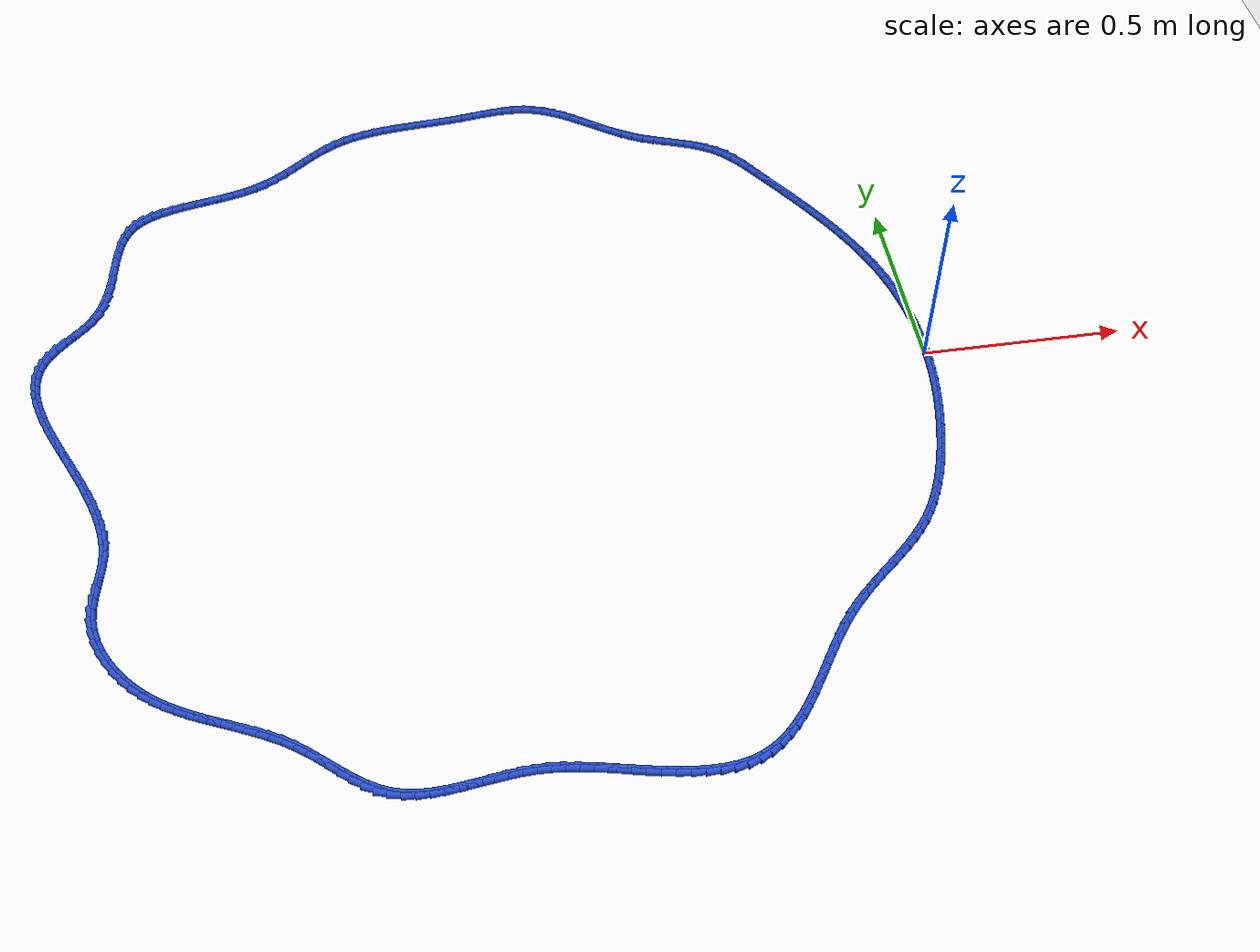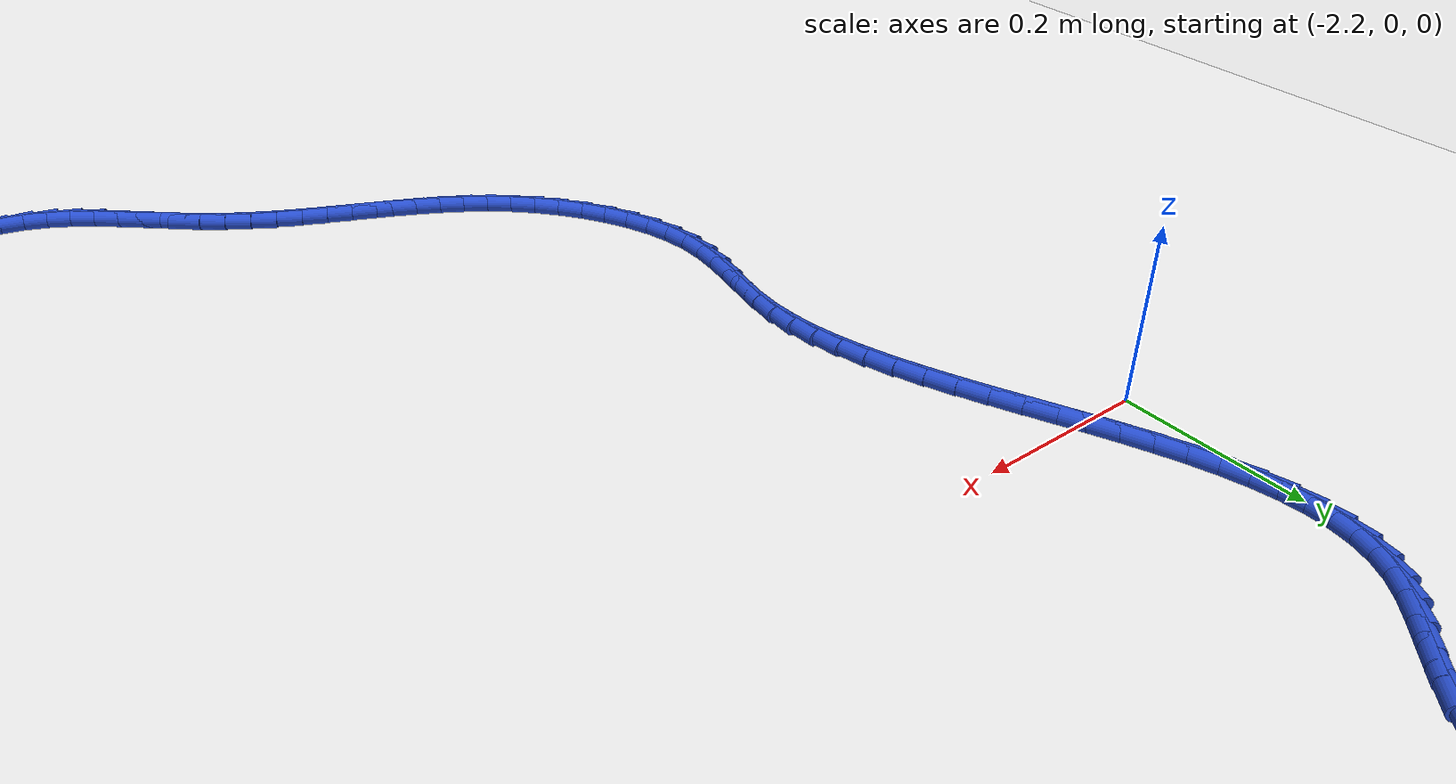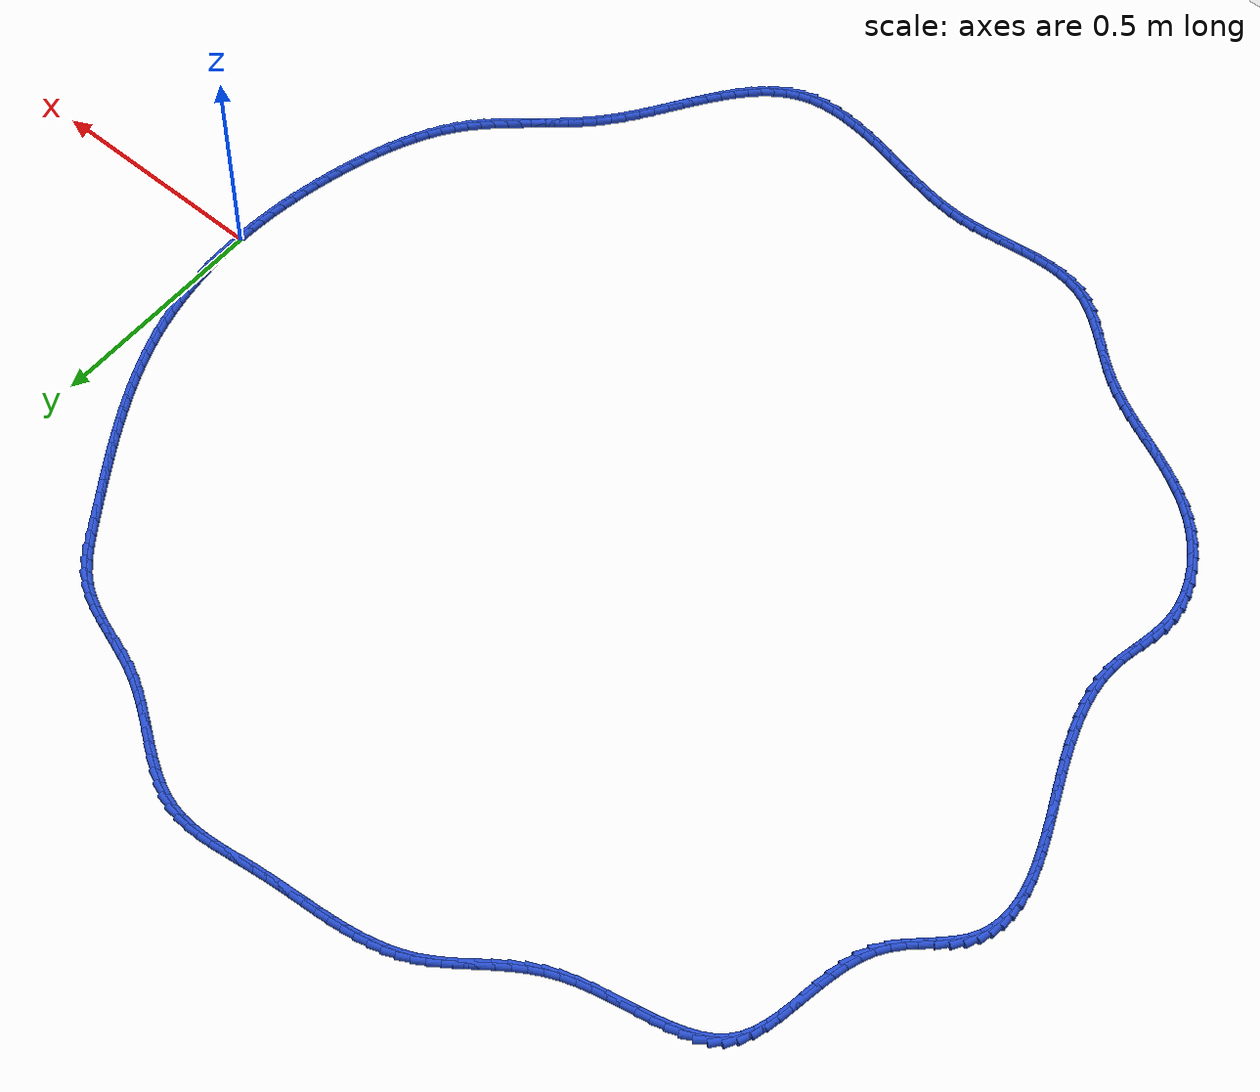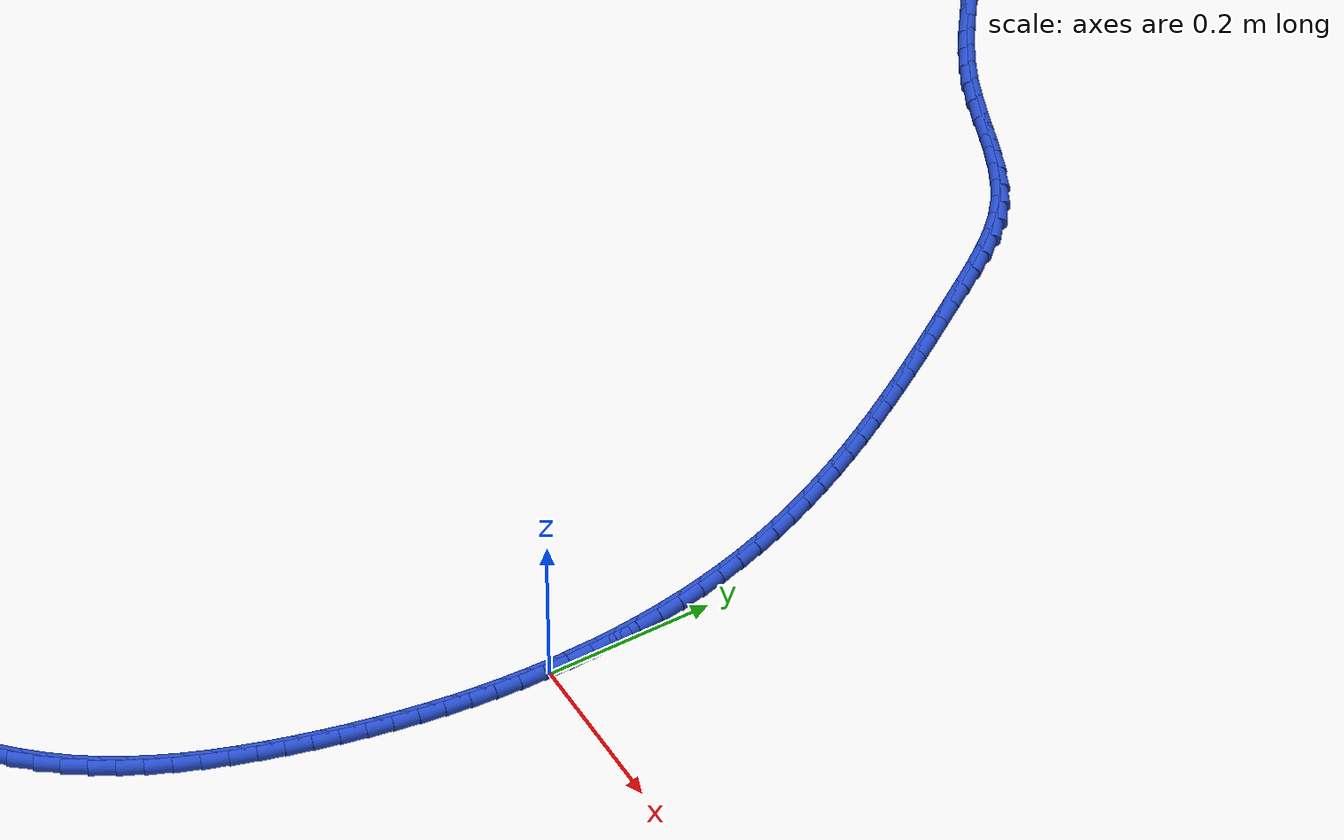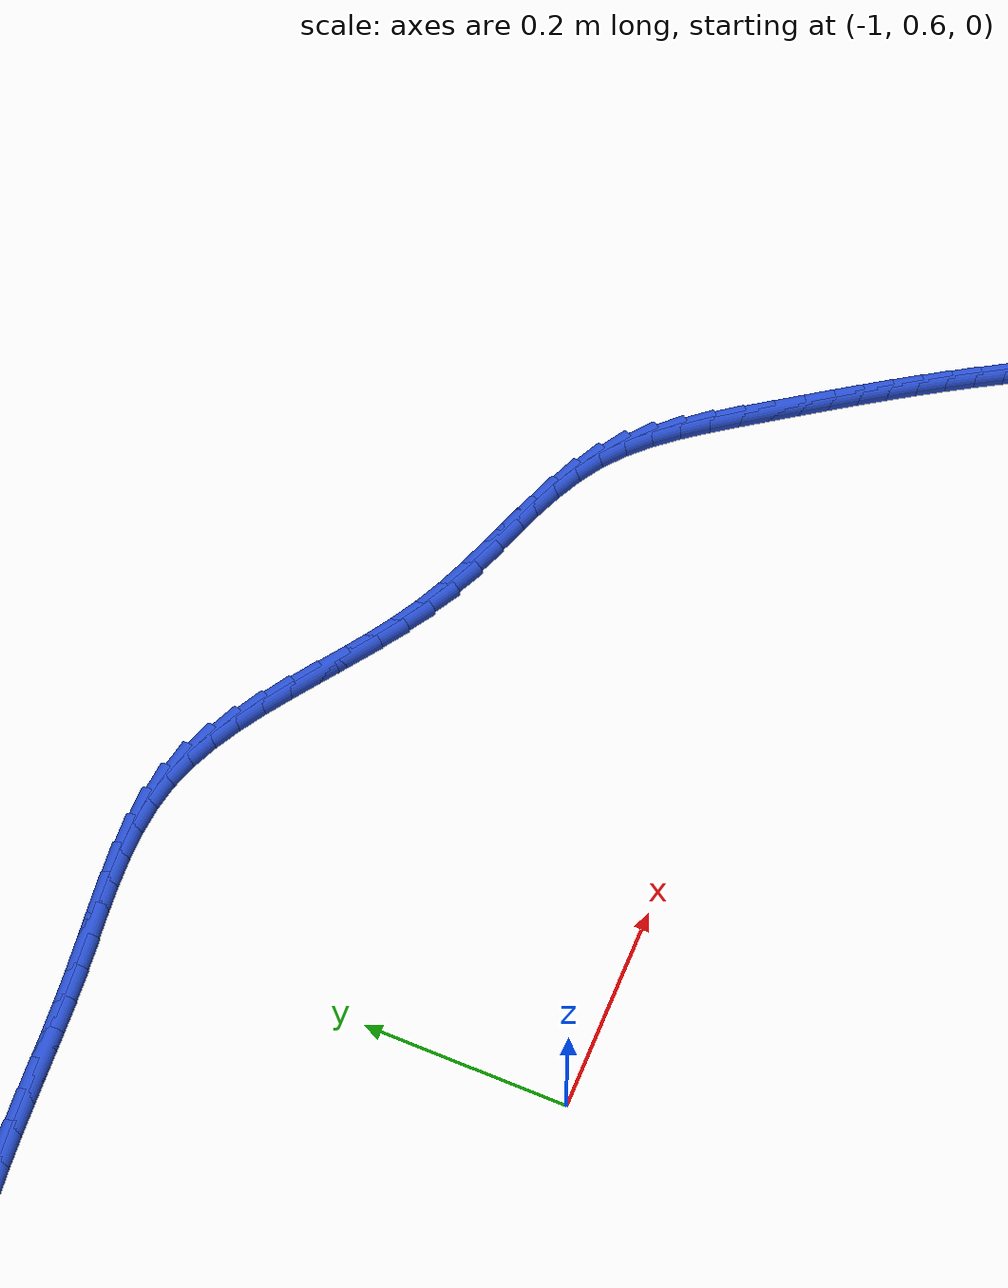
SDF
<sdf version="1.6">
 <world name="default">
  <light name="sun" type="directional">
   <pose>0 0 10 0 -0 0</pose>
   <diffuse>0.8 0.8 0.8 1</diffuse>
   <specular>0.2 0.2 0.2 1</specular>
   <attenuation>
    <range>1000</range>
    <constant>0.9</constant>
    <linear>0.01</linear>
    <quadratic>0.001</quadratic>
   </attenuation>
   <direction>-0.5 0.1 -0.9</direction>
  </light>
  <model name="ground_plane">
   <static>1</static>
   <link name="link">
    <collision name="collision">
     <geometry><plane><normal>0 0 1</normal><size>100 100</size></plane></geometry>
     <surface><friction><ode><mu>100</mu><mu2>50</mu2></ode></friction></surface>
    </collision>
    <visual name="visual">
     <cast_shadows>0</cast_shadows>
     <geometry><plane><normal>0 0 1</normal><size>100 100</size></plane></geometry>
     <material>
      <script><uri>file://media/materials/scripts/gazebo.material</uri><name>Gazebo/WhiteGlow</name></script>
     </material>
    </visual>
   </link>
  </model>
  <gravity>0 0 -9.8</gravity>
  <magnetic_field>6e-06 2.3e-05 -4.2e-05</magnetic_field>
  <atmosphere type="adiabatic"/>
  <physics name="default_physics" default="0" type="ode">
   <max_step_size>0.001</max_step_size>
   <real_time_factor>1</real_time_factor>
   <real_time_update_rate>1000</real_time_update_rate>
  </physics>
  <scene><ambient>0.4 0.4 0.4 1</ambient><background>0.7 0.7 0.7 1</background><shadows>1</shadows></scene>
  <spherical_coordinates>
   <surface_model>EARTH_WGS84</surface_model>
   <latitude_deg>0</latitude_deg>
   <longitude_deg>0</longitude_deg>
   <elevation>0</elevation>
   <heading_deg>0</heading_deg>
  </spherical_coordinates>
  <model name="line">
   <link name="link_0">
    <pose>-6.071532165918825e-18 9.020562075079397e-17 0.01 0 1.57 -1.5642609833262457</pose>
    <collision name="collision">
     <geometry><cylinder><radius>0.01</radius><length>0.08</length></cylinder></geometry>
    </collision>
    <visual name="visual">
     <material>
      <script><name>Gazebo/Blue</name><uri>file://media/materials/scripts/gazebo.material</uri></script>
     </material>
     <geometry><cylinder><radius>0.01</radius><length>0.08</length></cylinder></geometry>
    </visual>
   </link>
   <link name="link_1">
    <pose>-0.00019538533817303858 0.02989629503328875 0.01 0 1.57 -1.533442080625066</pose>
    <collision name="collision">
     <geometry><cylinder><radius>0.01</radius><length>0.08</length></cylinder></geometry>
    </collision>
    <visual name="visual">
     <material>
      <script><name>Gazebo/Blue</name><uri>file://media/materials/scripts/gazebo.material</uri></script>
     </material>
     <geometry><cylinder><radius>0.01</radius><length>0.08</length></cylinder></geometry>
    </visual>
   </link>
   <link name="link_2">
    <pose>-0.001314598239402544 0.05984449120298663 0.01 0 1.57 -1.5023022908751729</pose>
    <collision name="collision">
     <geometry><cylinder><radius>0.01</radius><length>0.08</length></cylinder></geometry>
    </collision>
    <visual name="visual">
     <material>
      <script><name>Gazebo/Blue</name><uri>file://media/materials/scripts/gazebo.material</uri></script>
     </material>
     <geometry><cylinder><radius>0.01</radius><length>0.08</length></cylinder></geometry>
    </visual>
   </link>
   <link name="link_3">
    <pose>-0.003368566965591087 0.08978513749059894 0.01 0 1.57 -1.4707204219598675</pose>
    <collision name="collision">
     <geometry><cylinder><radius>0.01</radius><length>0.08</length></cylinder></geometry>
    </collision>
    <visual name="visual">
     <material>
      <script><name>Gazebo/Blue</name><uri>file://media/materials/scripts/gazebo.material</uri></script>
     </material>
     <geometry><cylinder><radius>0.01</radius><length>0.08</length></cylinder></geometry>
    </visual>
   </link>
   <link name="link_4">
    <pose>-0.006368219778641236 0.11965878287763072 0.01 0 1.57 -1.438576005103352</pose>
    <collision name="collision">
     <geometry><cylinder><radius>0.01</radius><length>0.08</length></cylinder></geometry>
    </collision>
    <visual name="visual">
     <material>
      <script><name>Gazebo/Blue</name><uri>file://media/materials/scripts/gazebo.material</uri></script>
     </material>
     <geometry><cylinder><radius>0.01</radius><length>0.08</length></cylinder></geometry>
    </visual>
   </link>
   <link name="link_5">
    <pose>-0.010324484940455559 0.1494059763455871 0.01 0 1.57 -1.4057488932148994</pose>
    <collision name="collision">
     <geometry><cylinder><radius>0.01</radius><length>0.08</length></cylinder></geometry>
    </collision>
    <visual name="visual">
     <material>
      <script><name>Gazebo/Blue</name><uri>file://media/materials/scripts/gazebo.material</uri></script>
     </material>
     <geometry><cylinder><radius>0.01</radius><length>0.08</length></cylinder></geometry>
    </visual>
   </link>
   <link name="link_6">
    <pose>-0.015248290712936626 0.1789672668759733 0.01 0 1.57 -1.3721190641973917</pose>
    <collision name="collision">
     <geometry><cylinder><radius>0.01</radius><length>0.08</length></cylinder></geometry>
    </collision>
    <visual name="visual">
     <material>
      <script><name>Gazebo/Blue</name><uri>file://media/materials/scripts/gazebo.material</uri></script>
     </material>
     <geometry><cylinder><radius>0.01</radius><length>0.08</length></cylinder></geometry>
    </visual>
   </link>
   <link name="link_7">
    <pose>-0.021150565357986997 0.2082832034502943 0.01 0 1.57 -1.3375666687550478</pose>
    <collision name="collision">
     <geometry><cylinder><radius>0.01</radius><length>0.08</length></cylinder></geometry>
    </collision>
    <visual name="visual">
     <material>
      <script><name>Gazebo/Blue</name><uri>file://media/materials/scripts/gazebo.material</uri></script>
     </material>
     <geometry><cylinder><radius>0.01</radius><length>0.08</length></cylinder></geometry>
    </visual>
   </link>
   <link name="link_8">
    <pose>-0.028042237137509238 0.23729433505005518 0.01 0 1.57 -1.3019723716880667</pose>
    <collision name="collision">
     <geometry><cylinder><radius>0.01</radius><length>0.08</length></cylinder></geometry>
    </collision>
    <visual name="visual">
     <material>
      <script><name>Gazebo/Blue</name><uri>file://media/materials/scripts/gazebo.material</uri></script>
     </material>
     <geometry><cylinder><radius>0.01</radius><length>0.08</length></cylinder></geometry>
    </visual>
   </link>
   <link name="link_9">
    <pose>-0.03593423431340593 0.2659412106567612 0.01 0 1.57 -1.2655545698948552</pose>
    <collision name="collision">
     <geometry><cylinder><radius>0.01</radius><length>0.08</length></cylinder></geometry>
    </collision>
    <visual name="visual">
     <material>
      <script><name>Gazebo/Blue</name><uri>file://media/materials/scripts/gazebo.material</uri></script>
     </material>
     <geometry><cylinder><radius>0.01</radius><length>0.08</length></cylinder></geometry>
    </visual>
   </link>
   <link name="link_10">
    <pose>-0.044830068911962444 0.29417398166767234 0.01 0 1.57 -1.230315160714265</pose>
    <collision name="collision">
     <geometry><cylinder><radius>0.01</radius><length>0.08</length></cylinder></geometry>
    </collision>
    <visual name="visual">
     <material>
      <script><name>Gazebo/Blue</name><uri>file://media/materials/scripts/gazebo.material</uri></script>
     </material>
     <geometry><cylinder><radius>0.01</radius><length>0.08</length></cylinder></geometry>
    </visual>
   </link>
   <link name="link_11">
    <pose>-0.05468849212050699 0.3220007550531169 0.01 0 1.57 -1.1971280903031472</pose>
    <collision name="collision">
     <geometry><cylinder><radius>0.01</radius><length>0.08</length></cylinder></geometry>
    </collision>
    <visual name="visual">
     <material>
      <script><name>Gazebo/Blue</name><uri>file://media/materials/scripts/gazebo.material</uri></script>
     </material>
     <geometry><cylinder><radius>0.01</radius><length>0.08</length></cylinder></geometry>
    </visual>
   </link>
   <link name="link_12">
    <pose>-0.06545154566685278 0.3494512729074383 0.01 0 1.57 -1.166101578099795</pose>
    <collision name="collision">
     <geometry><cylinder><radius>0.01</radius><length>0.08</length></cylinder></geometry>
    </collision>
    <visual name="visual">
     <material>
      <script><name>Gazebo/Blue</name><uri>file://media/materials/scripts/gazebo.material</uri></script>
     </material>
     <geometry><cylinder><radius>0.01</radius><length>0.08</length></cylinder></geometry>
    </visual>
   </link>
   <link name="link_13">
    <pose>-0.07706124258835327 0.3765553144728994 0.01 0 1.57 -1.1373130696278033</pose>
    <collision name="collision">
     <geometry><cylinder><radius>0.01</radius><length>0.08</length></cylinder></geometry>
    </collision>
    <visual name="visual">
     <material>
      <script><name>Gazebo/Blue</name><uri>file://media/materials/scripts/gazebo.material</uri></script>
     </material>
     <geometry><cylinder><radius>0.01</radius><length>0.08</length></cylinder></geometry>
    </visual>
   </link>
   <link name="link_14">
    <pose>-0.08945959592236201 0.40334265899176297 0.01 0 1.57 -1.110813930483149</pose>
    <collision name="collision">
     <geometry><cylinder><radius>0.01</radius><length>0.08</length></cylinder></geometry>
    </collision>
    <visual name="visual">
     <material>
      <script><name>Gazebo/Blue</name><uri>file://media/materials/scripts/gazebo.material</uri></script>
     </material>
     <geometry><cylinder><radius>0.01</radius><length>0.08</length></cylinder></geometry>
    </visual>
   </link>
   <link name="link_15">
    <pose>-0.10258861870623243 0.4298430857062916 0.01 0 1.57 -1.0866333033812545</pose>
    <collision name="collision">
     <geometry><cylinder><radius>0.01</radius><length>0.08</length></cylinder></geometry>
    </collision>
    <visual name="visual">
     <material>
      <script><name>Gazebo/Blue</name><uri>file://media/materials/scripts/gazebo.material</uri></script>
     </material>
     <geometry><cylinder><radius>0.01</radius><length>0.08</length></cylinder></geometry>
    </visual>
   </link>
   <link name="link_16">
    <pose>-0.11639032397731805 0.456086373858748 0.01 0 1.57 -1.0647821116608314</pose>
    <collision name="collision">
     <geometry><cylinder><radius>0.01</radius><length>0.08</length></cylinder></geometry>
    </collision>
    <visual name="visual">
     <material>
      <script><name>Gazebo/Blue</name><uri>file://media/materials/scripts/gazebo.material</uri></script>
     </material>
     <geometry><cylinder><radius>0.01</radius><length>0.08</length></cylinder></geometry>
    </visual>
   </link>
   <link name="link_17">
    <pose>-0.13080672477297237 0.4821023026913951 0.01 0 1.57 -1.0452569621738448</pose>
    <collision name="collision">
     <geometry><cylinder><radius>0.01</radius><length>0.08</length></cylinder></geometry>
    </collision>
    <visual name="visual">
     <material>
      <script><name>Gazebo/Blue</name><uri>file://media/materials/scripts/gazebo.material</uri></script>
     </material>
     <geometry><cylinder><radius>0.01</radius><length>0.08</length></cylinder></geometry>
    </visual>
   </link>
   <link name="link_18">
    <pose>-0.14577983413054885 0.5079206514464956 0.01 0 1.57 -1.0280437732857843</pose>
    <collision name="collision">
     <geometry><cylinder><radius>0.01</radius><length>0.08</length></cylinder></geometry>
    </collision>
    <visual name="visual">
     <material>
      <script><name>Gazebo/Blue</name><uri>file://media/materials/scripts/gazebo.material</uri></script>
     </material>
     <geometry><cylinder><radius>0.01</radius><length>0.08</length></cylinder></geometry>
    </visual>
   </link>
   <link name="link_19">
    <pose>-0.16125166508740094 0.533571199366312 0.01 0 1.57 -1.0131210190796889</pose>
    <collision name="collision">
     <geometry><cylinder><radius>0.01</radius><length>0.08</length></cylinder></geometry>
    </collision>
    <visual name="visual">
     <material>
      <script><name>Gazebo/Blue</name><uri>file://media/materials/scripts/gazebo.material</uri></script>
     </material>
     <geometry><cylinder><radius>0.01</radius><length>0.08</length></cylinder></geometry>
    </visual>
   </link>
   <link name="link_20">
    <pose>-0.17716423068088227 0.5590837256931075 0.01 0 1.57 -1.00046253402051</pose>
    <collision name="collision">
     <geometry><cylinder><radius>0.01</radius><length>0.08</length></cylinder></geometry>
    </collision>
    <visual name="visual">
     <material>
      <script><name>Gazebo/Blue</name><uri>file://media/materials/scripts/gazebo.material</uri></script>
     </material>
     <geometry><cylinder><radius>0.01</radius><length>0.08</length></cylinder></geometry>
    </visual>
   </link>
   <link name="link_21">
    <pose>-0.19345954394834622 0.5844880096691445 0.01 0 1.57 -0.9900398618783286</pose>
    <collision name="collision">
     <geometry><cylinder><radius>0.01</radius><length>0.08</length></cylinder></geometry>
    </collision>
    <visual name="visual">
     <material>
      <script><name>Gazebo/Blue</name><uri>file://media/materials/scripts/gazebo.material</uri></script>
     </material>
     <geometry><cylinder><radius>0.01</radius><length>0.08</length></cylinder></geometry>
    </visual>
   </link>
   <link name="link_22">
    <pose>-0.21007961792714636 0.6098138305366858 0.01 0 1.57 -0.9818241594196397</pose>
    <collision name="collision">
     <geometry><cylinder><radius>0.01</radius><length>0.08</length></cylinder></geometry>
    </collision>
    <visual name="visual">
     <material>
      <script><name>Gazebo/Blue</name><uri>file://media/materials/scripts/gazebo.material</uri></script>
     </material>
     <geometry><cylinder><radius>0.01</radius><length>0.08</length></cylinder></geometry>
    </visual>
   </link>
   <link name="link_23">
    <pose>-0.22696646565463602 0.6350909675379942 0.01 0 1.57 -0.9757876812215632</pose>
    <collision name="collision">
     <geometry><cylinder><radius>0.01</radius><length>0.08</length></cylinder></geometry>
    </collision>
    <visual name="visual">
     <material>
      <script><name>Gazebo/Blue</name><uri>file://media/materials/scripts/gazebo.material</uri></script>
     </material>
     <geometry><cylinder><radius>0.01</radius><length>0.08</length></cylinder></geometry>
    </visual>
   </link>
   <link name="link_24">
    <pose>-0.24406210016816893 0.6603491999153326 0.01 0 1.57 -0.9719048793293218</pose>
    <collision name="collision">
     <geometry><cylinder><radius>0.01</radius><length>0.08</length></cylinder></geometry>
    </collision>
    <visual name="visual">
     <material>
      <script><name>Gazebo/Blue</name><uri>file://media/materials/scripts/gazebo.material</uri></script>
     </material>
     <geometry><cylinder><radius>0.01</radius><length>0.08</length></cylinder></geometry>
    </visual>
   </link>
   <link name="link_25">
    <pose>-0.26130853450509817 0.6856183069109629 0.01 0 1.57 -0.9700452745738253</pose>
    <collision name="collision">
     <geometry><cylinder><radius>0.01</radius><length>0.08</length></cylinder></geometry>
    </collision>
    <visual name="visual">
     <material>
      <script><name>Gazebo/Blue</name><uri>file://media/materials/scripts/gazebo.material</uri></script>
     </material>
     <geometry><cylinder><radius>0.01</radius><length>0.08</length></cylinder></geometry>
    </visual>
   </link>
   <link name="link_26">
    <pose>-0.27864981983011977 0.7109251870233977 0.01 0 1.57 -0.9614957935794757</pose>
    <collision name="collision">
     <geometry><cylinder><radius>0.01</radius><length>0.08</length></cylinder></geometry>
    </collision>
    <visual name="visual">
     <material>
      <script><name>Gazebo/Blue</name><uri>file://media/materials/scripts/gazebo.material</uri></script>
     </material>
     <geometry><cylinder><radius>0.01</radius><length>0.08</length></cylinder></geometry>
    </visual>
   </link>
   <link name="link_27">
    <pose>-0.2961941565231202 0.7360647258556623 0.01 0 1.57 -0.9309521675213168</pose>
    <collision name="collision">
     <geometry><cylinder><radius>0.01</radius><length>0.08</length></cylinder></geometry>
    </collision>
    <visual name="visual">
     <material>
      <script><name>Gazebo/Blue</name><uri>file://media/materials/scripts/gazebo.material</uri></script>
     </material>
     <geometry><cylinder><radius>0.01</radius><length>0.08</length></cylinder></geometry>
    </visual>
   </link>
   <link name="link_28">
    <pose>-0.3143317075412472 0.7604332755551562 0.01 0 1.57 -0.8755480288631161</pose>
    <collision name="collision">
     <geometry><cylinder><radius>0.01</radius><length>0.08</length></cylinder></geometry>
    </collision>
    <visual name="visual">
     <material>
      <script><name>Gazebo/Blue</name><uri>file://media/materials/scripts/gazebo.material</uri></script>
     </material>
     <geometry><cylinder><radius>0.01</radius><length>0.08</length></cylinder></geometry>
    </visual>
   </link>
   <link name="link_29">
    <pose>-0.3334804207619129 0.7833879163190962 0.01 0 1.57 -0.793113111554915</pose>
    <collision name="collision">
     <geometry><cylinder><radius>0.01</radius><length>0.08</length></cylinder></geometry>
    </collision>
    <visual name="visual">
     <material>
      <script><name>Gazebo/Blue</name><uri>file://media/materials/scripts/gazebo.material</uri></script>
     </material>
     <geometry><cylinder><radius>0.01</radius><length>0.08</length></cylinder></geometry>
    </visual>
   </link>
   <link name="link_30">
    <pose>-0.35405824406252967 0.8042857283446996 0.01 0 1.57 -0.6818845650359583</pose>
    <collision name="collision">
     <geometry><cylinder><radius>0.01</radius><length>0.08</length></cylinder></geometry>
    </collision>
    <visual name="visual">
     <material>
      <script><name>Gazebo/Blue</name><uri>file://media/materials/scripts/gazebo.material</uri></script>
     </material>
     <geometry><cylinder><radius>0.01</radius><length>0.08</length></cylinder></geometry>
    </visual>
   </link>
   <link name="link_31">
    <pose>-0.3764806287589229 0.8224878408759467 0.01 0 1.57 -0.5596379906452319</pose>
    <collision name="collision">
     <geometry><cylinder><radius>0.01</radius><length>0.08</length></cylinder></geometry>
    </collision>
    <visual name="visual">
     <material>
      <script><name>Gazebo/Blue</name><uri>file://media/materials/scripts/gazebo.material</uri></script>
     </material>
     <geometry><cylinder><radius>0.01</radius><length>0.08</length></cylinder></geometry>
    </visual>
   </link>
   <link name="link_32">
    <pose>-0.400898545392823 0.8377843311258923 0.01 0 1.57 -0.46205582248289456</pose>
    <collision name="collision">
     <geometry><cylinder><radius>0.01</radius><length>0.08</length></cylinder></geometry>
    </collision>
    <visual name="visual">
     <material>
      <script><name>Gazebo/Blue</name><uri>file://media/materials/scripts/gazebo.material</uri></script>
     </material>
     <geometry><cylinder><radius>0.01</radius><length>0.08</length></cylinder></geometry>
    </visual>
   </link>
   <link name="link_33">
    <pose>-0.426968380112761 0.8507674176795854 0.01 0 1.57 -0.3936970724352948</pose>
    <collision name="collision">
     <geometry><cylinder><radius>0.01</radius><length>0.08</length></cylinder></geometry>
    </collision>
    <visual name="visual">
     <material>
      <script><name>Gazebo/Blue</name><uri>file://media/materials/scripts/gazebo.material</uri></script>
     </material>
     <geometry><cylinder><radius>0.01</radius><length>0.08</length></cylinder></geometry>
    </visual>
   </link>
   <link name="link_34">
    <pose>-0.4542922693412246 0.8621173040044866 0.01 0 1.57 -0.3534513228596217</pose>
    <collision name="collision">
     <geometry><cylinder><radius>0.01</radius><length>0.08</length></cylinder></geometry>
    </collision>
    <visual name="visual">
     <material>
      <script><name>Gazebo/Blue</name><uri>file://media/materials/scripts/gazebo.material</uri></script>
     </material>
     <geometry><cylinder><radius>0.01</radius><length>0.08</length></cylinder></geometry>
    </visual>
   </link>
   <link name="link_35">
    <pose>-0.48247234950070156 0.8725141935680573 0.01 0 1.57 -0.33980246243570883</pose>
    <collision name="collision">
     <geometry><cylinder><radius>0.01</radius><length>0.08</length></cylinder></geometry>
    </collision>
    <visual name="visual">
     <material>
      <script><name>Gazebo/Blue</name><uri>file://media/materials/scripts/gazebo.material</uri></script>
     </material>
     <geometry><cylinder><radius>0.01</radius><length>0.08</length></cylinder></geometry>
    </visual>
   </link>
   <link name="link_36">
    <pose>-0.5111107570136796 0.8826382898377585 0.01 0 1.57 -0.35170851816649323</pose>
    <collision name="collision">
     <geometry><cylinder><radius>0.01</radius><length>0.08</length></cylinder></geometry>
    </collision>
    <visual name="visual">
     <material>
      <script><name>Gazebo/Blue</name><uri>file://media/materials/scripts/gazebo.material</uri></script>
     </material>
     <geometry><cylinder><radius>0.01</radius><length>0.08</length></cylinder></geometry>
    </visual>
   </link>
   <link name="link_37">
    <pose>-0.5398096283026466 0.8931697962810513 0.01 0 1.57 -0.3888230230529627</pose>
    <collision name="collision">
     <geometry><cylinder><radius>0.01</radius><length>0.08</length></cylinder></geometry>
    </collision>
    <visual name="visual">
     <material>
      <script><name>Gazebo/Blue</name><uri>file://media/materials/scripts/gazebo.material</uri></script>
     </material>
     <geometry><cylinder><radius>0.01</radius><length>0.08</length></cylinder></geometry>
    </visual>
   </link>
   <link name="link_38">
    <pose>-0.56817109979009 0.9047889163653963 0.01 0 1.57 -0.4507395362927816</pose>
    <collision name="collision">
     <geometry><cylinder><radius>0.01</radius><length>0.08</length></cylinder></geometry>
    </collision>
    <visual name="visual">
     <material>
      <script><name>Gazebo/Blue</name><uri>file://media/materials/scripts/gazebo.material</uri></script>
     </material>
     <geometry><cylinder><radius>0.01</radius><length>0.08</length></cylinder></geometry>
    </visual>
   </link>
   <link name="link_39">
    <pose>-0.595803769565545 0.918162230282935 0.01 0 1.57 -0.5189964842098511</pose>
    <collision name="collision">
     <geometry><cylinder><radius>0.01</radius><length>0.08</length></cylinder></geometry>
    </collision>
    <visual name="visual">
     <material>
      <script><name>Gazebo/Blue</name><uri>file://media/materials/scripts/gazebo.material</uri></script>
     </material>
     <geometry><cylinder><radius>0.01</radius><length>0.08</length></cylinder></geometry>
    </visual>
   </link>
   <link name="link_40">
    <pose>-0.6225585781766925 0.9334453822699332 0.01 0 1.57 -0.5701683551198653</pose>
    <collision name="collision">
     <geometry><cylinder><radius>0.01</radius><length>0.08</length></cylinder></geometry>
    </collision>
    <visual name="visual">
     <material>
      <script><name>Gazebo/Blue</name><uri>file://media/materials/scripts/gazebo.material</uri></script>
     </material>
     <geometry><cylinder><radius>0.01</radius><length>0.08</length></cylinder></geometry>
    </visual>
   </link>
   <link name="link_41">
    <pose>-0.6485962486228254 0.9501408953793627 0.01 0 1.57 -0.6032331998880286</pose>
    <collision name="collision">
     <geometry><cylinder><radius>0.01</radius><length>0.08</length></cylinder></geometry>
    </collision>
    <visual name="visual">
     <material>
      <script><name>Gazebo/Blue</name><uri>file://media/materials/scripts/gazebo.material</uri></script>
     </material>
     <geometry><cylinder><radius>0.01</radius><length>0.08</length></cylinder></geometry>
    </visual>
   </link>
   <link name="link_42">
    <pose>-0.6740977089537417 0.9677086939100493 0.01 0 1.57 -0.6186269044177696</pose>
    <collision name="collision">
     <geometry><cylinder><radius>0.01</radius><length>0.08</length></cylinder></geometry>
    </collision>
    <visual name="visual">
     <material>
      <script><name>Gazebo/Blue</name><uri>file://media/materials/scripts/gazebo.material</uri></script>
     </material>
     <geometry><cylinder><radius>0.01</radius><length>0.08</length></cylinder></geometry>
    </visual>
   </link>
   <link name="link_43">
    <pose>-0.6992438872192397 0.9856087021608192 0.01 0 1.57 -0.6163973742456529</pose>
    <collision name="collision">
     <geometry><cylinder><radius>0.01</radius><length>0.08</length></cylinder></geometry>
    </collision>
    <visual name="visual">
     <material>
      <script><name>Gazebo/Blue</name><uri>file://media/materials/scripts/gazebo.material</uri></script>
     </material>
     <geometry><cylinder><radius>0.01</radius><length>0.08</length></cylinder></geometry>
    </visual>
   </link>
   <link name="link_44">
    <pose>-0.7242157114691179 1.0033008444304992 0.01 0 1.57 -0.5960503644967289</pose>
    <collision name="collision">
     <geometry><cylinder><radius>0.01</radius><length>0.08</length></cylinder></geometry>
    </collision>
    <visual name="visual">
     <material>
      <script><name>Gazebo/Blue</name><uri>file://media/materials/scripts/gazebo.material</uri></script>
     </material>
     <geometry><cylinder><radius>0.01</radius><length>0.08</length></cylinder></geometry>
    </visual>
   </link>
   <link name="link_45">
    <pose>-0.7491941097531744 1.020245045017915 0.01 0 1.57 -0.5565248570679779</pose>
    <collision name="collision">
     <geometry><cylinder><radius>0.01</radius><length>0.08</length></cylinder></geometry>
    </collision>
    <visual name="visual">
     <material>
      <script><name>Gazebo/Blue</name><uri>file://media/materials/scripts/gazebo.material</uri></script>
     </material>
     <geometry><cylinder><radius>0.01</radius><length>0.08</length></cylinder></geometry>
    </visual>
   </link>
   <link name="link_46">
    <pose>-0.7743600101212078 1.035901228221893 0.01 0 1.57 -0.4963317432481884</pose>
    <collision name="collision">
     <geometry><cylinder><radius>0.01</radius><length>0.08</length></cylinder></geometry>
    </collision>
    <visual name="visual">
     <material>
      <script><name>Gazebo/Blue</name><uri>file://media/materials/scripts/gazebo.material</uri></script>
     </material>
     <geometry><cylinder><radius>0.01</radius><length>0.08</length></cylinder></geometry>
    </visual>
   </link>
   <link name="link_47">
    <pose>-0.7998943406230158 1.0497293183412593 0.01 0 1.57 -0.41396386690748427</pose>
    <collision name="collision">
     <geometry><cylinder><radius>0.01</radius><length>0.08</length></cylinder></geometry>
    </collision>
    <visual name="visual">
     <material>
      <script><name>Gazebo/Blue</name><uri>file://media/materials/scripts/gazebo.material</uri></script>
     </material>
     <geometry><cylinder><radius>0.01</radius><length>0.08</length></cylinder></geometry>
    </visual>
   </link>
   <link name="link_48">
    <pose>-0.8259780293083971 1.0611892396748406 0.01 0 1.57 -0.3087285073231329</pose>
    <collision name="collision">
     <geometry><cylinder><radius>0.01</radius><length>0.08</length></cylinder></geometry>
    </collision>
    <visual name="visual">
     <material>
      <script><name>Gazebo/Blue</name><uri>file://media/materials/scripts/gazebo.material</uri></script>
     </material>
     <geometry><cylinder><radius>0.01</radius><length>0.08</length></cylinder></geometry>
    </visual>
   </link>
   <link name="link_49">
    <pose>-0.8527920042271497 1.0697409165214624 0.01 0 1.57 -0.18549978592933278</pose>
    <collision name="collision">
     <geometry><cylinder><radius>0.01</radius><length>0.08</length></cylinder></geometry>
    </collision>
    <visual name="visual">
     <material>
      <script><name>Gazebo/Blue</name><uri>file://media/materials/scripts/gazebo.material</uri></script>
     </material>
     <geometry><cylinder><radius>0.01</radius><length>0.08</length></cylinder></geometry>
    </visual>
   </link>
   <link name="link_50">
    <pose>-0.8804926074394791 1.0749391335600345 0.01 0 1.57 -0.07438732127856906</pose>
    <collision name="collision">
     <geometry><cylinder><radius>0.01</radius><length>0.08</length></cylinder></geometry>
    </collision>
    <visual name="visual">
     <material>
      <script><name>Gazebo/Blue</name><uri>file://media/materials/scripts/gazebo.material</uri></script>
     </material>
     <geometry><cylinder><radius>0.01</radius><length>0.08</length></cylinder></geometry>
    </visual>
   </link>
   <link name="link_51">
    <pose>-0.909047368598283 1.077067172349929 0.01 0 1.57 0.01096945344798775</pose>
    <collision name="collision">
     <geometry><cylinder><radius>0.01</radius><length>0.08</length></cylinder></geometry>
    </collision>
    <visual name="visual">
     <material>
      <script><name>Gazebo/Blue</name><uri>file://media/materials/scripts/gazebo.material</uri></script>
     </material>
     <geometry><cylinder><radius>0.01</radius><length>0.08</length></cylinder></geometry>
    </visual>
   </link>
   <link name="link_52">
    <pose>-0.9383363279898737 1.0767458755861432 0.01 0 1.57 0.07170795489163372</pose>
    <collision name="collision">
     <geometry><cylinder><radius>0.01</radius><length>0.08</length></cylinder></geometry>
    </collision>
    <visual name="visual">
     <material>
      <script><name>Gazebo/Blue</name><uri>file://media/materials/scripts/gazebo.material</uri></script>
     </material>
     <geometry><cylinder><radius>0.01</radius><length>0.08</length></cylinder></geometry>
    </visual>
   </link>
   <link name="link_53">
    <pose>-0.9682390480073012 1.0745979298242332 0.01 0 1.57 0.10983072902592239</pose>
    <collision name="collision">
     <geometry><cylinder><radius>0.01</radius><length>0.08</length></cylinder></geometry>
    </collision>
    <visual name="visual">
     <material>
      <script><name>Gazebo/Blue</name><uri>file://media/materials/scripts/gazebo.material</uri></script>
     </material>
     <geometry><cylinder><radius>0.01</radius><length>0.08</length></cylinder></geometry>
    </visual>
   </link>
   <link name="link_54">
    <pose>-0.9986350910436159 1.0712460216197555 0.01 0 1.57 0.12714022182581228</pose>
    <collision name="collision">
     <geometry><cylinder><radius>0.01</radius><length>0.08</length></cylinder></geometry>
    </collision>
    <visual name="visual">
     <material>
      <script><name>Gazebo/Blue</name><uri>file://media/materials/scripts/gazebo.material</uri></script>
     </material>
     <geometry><cylinder><radius>0.01</radius><length>0.08</length></cylinder></geometry>
    </visual>
   </link>
   <link name="link_55">
    <pose>-1.0294040194918677 1.0673128375282663 0.01 0 1.57 0.12480254622907483</pose>
    <collision name="collision">
     <geometry><cylinder><radius>0.01</radius><length>0.08</length></cylinder></geometry>
    </collision>
    <visual name="visual">
     <material>
      <script><name>Gazebo/Blue</name><uri>file://media/materials/scripts/gazebo.material</uri></script>
     </material>
     <geometry><cylinder><radius>0.01</radius><length>0.08</length></cylinder></geometry>
    </visual>
   </link>
   <link name="link_56">
    <pose>-1.0604253957451064 1.0634210641053223 0.01 0 1.57 0.10520944080305453</pose>
    <collision name="collision">
     <geometry><cylinder><radius>0.01</radius><length>0.08</length></cylinder></geometry>
    </collision>
    <visual name="visual">
     <material>
      <script><name>Gazebo/Blue</name><uri>file://media/materials/scripts/gazebo.material</uri></script>
     </material>
     <geometry><cylinder><radius>0.01</radius><length>0.08</length></cylinder></geometry>
    </visual>
   </link>
   <link name="link_57">
    <pose>-1.0915800318354472 1.0601311545983771 0.01 0 1.57 0.0856828569405367</pose>
    <collision name="collision">
     <geometry><cylinder><radius>0.01</radius><length>0.08</length></cylinder></geometry>
    </collision>
    <visual name="visual">
     <material>
      <script><name>Gazebo/Blue</name><uri>file://media/materials/scripts/gazebo.material</uri></script>
     </material>
     <geometry><cylinder><radius>0.01</radius><length>0.08</length></cylinder></geometry>
    </visual>
   </link>
   <link name="link_58">
    <pose>-1.1227597945045655 1.0574530263716857 0.01 0 1.57 0.07521198966103324</pose>
    <collision name="collision">
     <geometry><cylinder><radius>0.01</radius><length>0.08</length></cylinder></geometry>
    </collision>
    <visual name="visual">
     <material>
      <script><name>Gazebo/Blue</name><uri>file://media/materials/scripts/gazebo.material</uri></script>
     </material>
     <geometry><cylinder><radius>0.01</radius><length>0.08</length></cylinder></geometry>
    </visual>
   </link>
   <link name="link_59">
    <pose>-1.1538623189325277 1.0551093226367927 0.01 0 1.57 0.07389194304261185</pose>
    <collision name="collision">
     <geometry><cylinder><radius>0.01</radius><length>0.08</length></cylinder></geometry>
    </collision>
    <visual name="visual">
     <material>
      <script><name>Gazebo/Blue</name><uri>file://media/materials/scripts/gazebo.material</uri></script>
     </material>
     <geometry><cylinder><radius>0.01</radius><length>0.08</length></cylinder></geometry>
    </visual>
   </link>
   <link name="link_60">
    <pose>-1.1847852903013625 1.0528201964560635 0.01 0 1.57 0.08187611354928515</pose>
    <collision name="collision">
     <geometry><cylinder><radius>0.01</radius><length>0.08</length></cylinder></geometry>
    </collision>
    <visual name="visual">
     <material>
      <script><name>Gazebo/Blue</name><uri>file://media/materials/scripts/gazebo.material</uri></script>
     </material>
     <geometry><cylinder><radius>0.01</radius><length>0.08</length></cylinder></geometry>
    </visual>
   </link>
   <link name="link_61">
    <pose>-1.2154263937931002 1.0503058008918624 0.01 0 1.57 0.09946641353819252</pose>
    <collision name="collision">
     <geometry><cylinder><radius>0.01</radius><length>0.08</length></cylinder></geometry>
    </collision>
    <visual name="visual">
     <material>
      <script><name>Gazebo/Blue</name><uri>file://media/materials/scripts/gazebo.material</uri></script>
     </material>
     <geometry><cylinder><radius>0.01</radius><length>0.08</length></cylinder></geometry>
    </visual>
   </link>
   <link name="link_62">
    <pose>-1.2456833145897697 1.047286289006554 0.01 0 1.57 0.12710484813376094</pose>
    <collision name="collision">
     <geometry><cylinder><radius>0.01</radius><length>0.08</length></cylinder></geometry>
    </collision>
    <visual name="visual">
     <material>
      <script><name>Gazebo/Blue</name><uri>file://media/materials/scripts/gazebo.material</uri></script>
     </material>
     <geometry><cylinder><radius>0.01</radius><length>0.08</length></cylinder></geometry>
    </visual>
   </link>
   <link name="link_63">
    <pose>-1.2754537378734025 1.043481813862503 0.01 0 1.57 0.1653381711260512</pose>
    <collision name="collision">
     <geometry><cylinder><radius>0.01</radius><length>0.08</length></cylinder></geometry>
    </collision>
    <visual name="visual">
     <material>
      <script><name>Gazebo/Blue</name><uri>file://media/materials/scripts/gazebo.material</uri></script>
     </material>
     <geometry><cylinder><radius>0.01</radius><length>0.08</length></cylinder></geometry>
    </visual>
   </link>
   <link name="link_64">
    <pose>-1.3046353488260265 1.0386125285220744 0.01 0 1.57 0.21474292622177274</pose>
    <collision name="collision">
     <geometry><cylinder><radius>0.01</radius><length>0.08</length></cylinder></geometry>
    </collision>
    <visual name="visual">
     <material>
      <script><name>Gazebo/Blue</name><uri>file://media/materials/scripts/gazebo.material</uri></script>
     </material>
     <geometry><cylinder><radius>0.01</radius><length>0.08</length></cylinder></geometry>
    </visual>
   </link>
   <link name="link_65">
    <pose>-1.3331258326296727 1.032398586047633 0.01 0 1.57 0.2757945706906577</pose>
    <collision name="collision">
     <geometry><cylinder><radius>0.01</radius><length>0.08</length></cylinder></geometry>
    </collision>
    <visual name="visual">
     <material>
      <script><name>Gazebo/Blue</name><uri>file://media/materials/scripts/gazebo.material</uri></script>
     </material>
     <geometry><cylinder><radius>0.01</radius><length>0.08</length></cylinder></geometry>
    </visual>
   </link>
   <link name="link_66">
    <pose>-1.3608228744663704 1.0245601395015425 0.01 0 1.57 0.34866804190396805</pose>
    <collision name="collision">
     <geometry><cylinder><radius>0.01</radius><length>0.08</length></cylinder></geometry>
    </collision>
    <visual name="visual">
     <material>
      <script><name>Gazebo/Blue</name><uri>file://media/materials/scripts/gazebo.material</uri></script>
     </material>
     <geometry><cylinder><radius>0.01</radius><length>0.08</length></cylinder></geometry>
    </visual>
   </link>
   <link name="link_67">
    <pose>-1.3876241595181495 1.0148173419461686 0.01 0 1.57 0.43297696151213083</pose>
    <collision name="collision">
     <geometry><cylinder><radius>0.01</radius><length>0.08</length></cylinder></geometry>
    </collision>
    <visual name="visual">
     <material>
      <script><name>Gazebo/Blue</name><uri>file://media/materials/scripts/gazebo.material</uri></script>
     </material>
     <geometry><cylinder><radius>0.01</radius><length>0.08</length></cylinder></geometry>
    </visual>
   </link>
   <link name="link_68">
    <pose>-1.41342737296704 1.0028903464438754 0.01 0 1.57 0.5221306683159997</pose>
    <collision name="collision">
     <geometry><cylinder><radius>0.01</radius><length>0.08</length></cylinder></geometry>
    </collision>
    <visual name="visual">
     <material>
      <script><name>Gazebo/Blue</name><uri>file://media/materials/scripts/gazebo.material</uri></script>
     </material>
     <geometry><cylinder><radius>0.01</radius><length>0.08</length></cylinder></geometry>
    </visual>
   </link>
   <link name="link_69">
    <pose>-1.4382013594802279 0.9886355321200069 0.01 0 1.57 0.5917377105811772</pose>
    <collision name="collision">
     <geometry><cylinder><radius>0.01</radius><length>0.08</length></cylinder></geometry>
    </collision>
    <visual name="visual">
     <material>
      <script><name>Gazebo/Blue</name><uri>file://media/materials/scripts/gazebo.material</uri></script>
     </material>
     <geometry><cylinder><radius>0.01</radius><length>0.08</length></cylinder></geometry>
    </visual>
   </link>
   <link name="link_70">
    <pose>-1.4622199861949203 0.9724932060206788 0.01 0 1.57 0.6358424477324445</pose>
    <collision name="collision">
     <geometry><cylinder><radius>0.01</radius><length>0.08</length></cylinder></geometry>
    </collision>
    <visual name="visual">
     <material>
      <script><name>Gazebo/Blue</name><uri>file://media/materials/scripts/gazebo.material</uri></script>
     </material>
     <geometry><cylinder><radius>0.01</radius><length>0.08</length></cylinder></geometry>
    </visual>
   </link>
   <link name="link_71">
    <pose>-1.4858388317384632 0.9550601017678538 0.01 0 1.57 0.6555038682424891</pose>
    <collision name="collision">
     <geometry><cylinder><radius>0.01</radius><length>0.08</length></cylinder></geometry>
    </collision>
    <visual name="visual">
     <material>
      <script><name>Gazebo/Blue</name><uri>file://media/materials/scripts/gazebo.material</uri></script>
     </material>
     <geometry><cylinder><radius>0.01</radius><length>0.08</length></cylinder></geometry>
    </visual>
   </link>
   <link name="link_72">
    <pose>-1.5094134756726505 0.9369329547723749 0.01 0 1.57 0.6517539682209945</pose>
    <collision name="collision">
     <geometry><cylinder><radius>0.01</radius><length>0.08</length></cylinder></geometry>
    </collision>
    <visual name="visual">
     <material>
      <script><name>Gazebo/Blue</name><uri>file://media/materials/scripts/gazebo.material</uri></script>
     </material>
     <geometry><cylinder><radius>0.01</radius><length>0.08</length></cylinder></geometry>
    </visual>
   </link>
   <link name="link_73">
    <pose>-1.533299497559273 0.9187085004450846 0.01 0 1.57 0.6252794125403575</pose>
    <collision name="collision">
     <geometry><cylinder><radius>0.01</radius><length>0.08</length></cylinder></geometry>
    </collision>
    <visual name="visual">
     <material>
      <script><name>Gazebo/Blue</name><uri>file://media/materials/scripts/gazebo.material</uri></script>
     </material>
     <geometry><cylinder><radius>0.01</radius><length>0.08</length></cylinder></geometry>
    </visual>
   </link>
   <link name="link_74">
    <pose>-1.557852476960125 0.9009834741968255 0.01 0 1.57 0.5765065148959982</pose>
    <collision name="collision">
     <geometry><cylinder><radius>0.01</radius><length>0.08</length></cylinder></geometry>
    </collision>
    <visual name="visual">
     <material>
      <script><name>Gazebo/Blue</name><uri>file://media/materials/scripts/gazebo.material</uri></script>
     </material>
     <geometry><cylinder><radius>0.01</radius><length>0.08</length></cylinder></geometry>
    </visual>
   </link>
   <link name="link_75">
    <pose>-1.5834279934369977 0.8843546114384404 0.01 0 1.57 0.5060126820836093</pose>
    <collision name="collision">
     <geometry><cylinder><radius>0.01</radius><length>0.08</length></cylinder></geometry>
    </collision>
    <visual name="visual">
     <material>
      <script><name>Gazebo/Blue</name><uri>file://media/materials/scripts/gazebo.material</uri></script>
     </material>
     <geometry><cylinder><radius>0.01</radius><length>0.08</length></cylinder></geometry>
    </visual>
   </link>
   <link name="link_76">
    <pose>-1.610381626551684 0.869418647580772 0.01 0 1.57 0.4160574497705836</pose>
    <collision name="collision">
     <geometry><cylinder><radius>0.01</radius><length>0.08</length></cylinder></geometry>
    </collision>
    <visual name="visual">
     <material>
      <script><name>Gazebo/Blue</name><uri>file://media/materials/scripts/gazebo.material</uri></script>
     </material>
     <geometry><cylinder><radius>0.01</radius><length>0.08</length></cylinder></geometry>
    </visual>
   </link>
   <link name="link_77">
    <pose>-1.6390522995078827 0.8567504524883015 0.01 0 1.57 0.3292026111108646</pose>
    <collision name="collision">
     <geometry><cylinder><radius>0.01</radius><length>0.08</length></cylinder></geometry>
    </collision>
    <visual name="visual">
     <material>
      <script><name>Gazebo/Blue</name><uri>file://media/materials/scripts/gazebo.material</uri></script>
     </material>
     <geometry><cylinder><radius>0.01</radius><length>0.08</length></cylinder></geometry>
    </visual>
   </link>
   <link name="link_78">
    <pose>-1.6693729146719765 0.8463918943097849 0.01 0 1.57 0.2653858996348108</pose>
    <collision name="collision">
     <geometry><cylinder><radius>0.01</radius><length>0.08</length></cylinder></geometry>
    </collision>
    <visual name="visual">
     <material>
      <script><name>Gazebo/Blue</name><uri>file://media/materials/scripts/gazebo.material</uri></script>
     </material>
     <geometry><cylinder><radius>0.01</radius><length>0.08</length></cylinder></geometry>
    </visual>
   </link>
   <link name="link_79">
    <pose>-1.7008571939319461 0.8378345642287214 0.01 0 1.57 0.2230253182194177</pose>
    <collision name="collision">
     <geometry><cylinder><radius>0.01</radius><length>0.08</length></cylinder></geometry>
    </collision>
    <visual name="visual">
     <material>
      <script><name>Gazebo/Blue</name><uri>file://media/materials/scripts/gazebo.material</uri></script>
     </material>
     <geometry><cylinder><radius>0.01</radius><length>0.08</length></cylinder></geometry>
    </visual>
   </link>
   <link name="link_80">
    <pose>-1.7329995700499943 0.8305447317303409 0.01 0 1.57 0.20028443890292583</pose>
    <collision name="collision">
     <geometry><cylinder><radius>0.01</radius><length>0.08</length></cylinder></geometry>
    </collision>
    <visual name="visual">
     <material>
      <script><name>Gazebo/Blue</name><uri>file://media/materials/scripts/gazebo.material</uri></script>
     </material>
     <geometry><cylinder><radius>0.01</radius><length>0.08</length></cylinder></geometry>
    </visual>
   </link>
   <link name="link_81">
    <pose>-1.7652944757883235 0.8239886662998727 0.01 0 1.57 0.19642170429190142</pose>
    <collision name="collision">
     <geometry><cylinder><radius>0.01</radius><length>0.08</length></cylinder></geometry>
    </collision>
    <visual name="visual">
     <material>
      <script><name>Gazebo/Blue</name><uri>file://media/materials/scripts/gazebo.material</uri></script>
     </material>
     <geometry><cylinder><radius>0.01</radius><length>0.08</length></cylinder></geometry>
    </visual>
   </link>
   <link name="link_82">
    <pose>-1.7972363439091374 0.8176326374225465 0.01 0 1.57 0.21198590512749693</pose>
    <collision name="collision">
     <geometry><cylinder><radius>0.01</radius><length>0.08</length></cylinder></geometry>
    </collision>
    <visual name="visual">
     <material>
      <script><name>Gazebo/Blue</name><uri>file://media/materials/scripts/gazebo.material</uri></script>
     </material>
     <geometry><cylinder><radius>0.01</radius><length>0.08</length></cylinder></geometry>
    </visual>
   </link>
   <link name="link_83">
    <pose>-1.8283196071746393 0.810942914583592 0.01 0 1.57 0.24900841222616585</pose>
    <collision name="collision">
     <geometry><cylinder><radius>0.01</radius><length>0.08</length></cylinder></geometry>
    </collision>
    <visual name="visual">
     <material>
      <script><name>Gazebo/Blue</name><uri>file://media/materials/scripts/gazebo.material</uri></script>
     </material>
     <geometry><cylinder><radius>0.01</radius><length>0.08</length></cylinder></geometry>
    </visual>
   </link>
   <link name="link_84">
    <pose>-1.8580386983470323 0.8033857672682391 0.01 0 1.57 0.31121712831345894</pose>
    <collision name="collision">
     <geometry><cylinder><radius>0.01</radius><length>0.08</length></cylinder></geometry>
    </collision>
    <visual name="visual">
     <material>
      <script><name>Gazebo/Blue</name><uri>file://media/materials/scripts/gazebo.material</uri></script>
     </material>
     <geometry><cylinder><radius>0.01</radius><length>0.08</length></cylinder></geometry>
    </visual>
   </link>
   <link name="link_85">
    <pose>-1.8858880501885191 0.794427464961717 0.01 0 1.57 0.4040869388895871</pose>
    <collision name="collision">
     <geometry><cylinder><radius>0.01</radius><length>0.08</length></cylinder></geometry>
    </collision>
    <visual name="visual">
     <material>
      <script><name>Gazebo/Blue</name><uri>file://media/materials/scripts/gazebo.material</uri></script>
     </material>
     <geometry><cylinder><radius>0.01</radius><length>0.08</length></cylinder></geometry>
    </visual>
   </link>
   <link name="link_86">
    <pose>-1.911362095461303 0.7835342771492555 0.01 0 1.57 0.5340786039586223</pose>
    <collision name="collision">
     <geometry><cylinder><radius>0.01</radius><length>0.08</length></cylinder></geometry>
    </collision>
    <visual name="visual">
     <material>
      <script><name>Gazebo/Blue</name><uri>file://media/materials/scripts/gazebo.material</uri></script>
     </material>
     <geometry><cylinder><radius>0.01</radius><length>0.08</length></cylinder></geometry>
    </visual>
   </link>
   <link name="link_87">
    <pose>-1.9339552669275868 0.7701724733160844 0.01 0 1.57 0.7056545061145715</pose>
    <collision name="collision">
     <geometry><cylinder><radius>0.01</radius><length>0.08</length></cylinder></geometry>
    </collision>
    <visual name="visual">
     <material>
      <script><name>Gazebo/Blue</name><uri>file://media/materials/scripts/gazebo.material</uri></script>
     </material>
     <geometry><cylinder><radius>0.01</radius><length>0.08</length></cylinder></geometry>
    </visual>
   </link>
   <link name="link_88">
    <pose>-1.9531619973495746 0.7538083229474327 0.01 0 1.57 0.9127495470192307</pose>
    <collision name="collision">
     <geometry><cylinder><radius>0.01</radius><length>0.08</length></cylinder></geometry>
    </collision>
    <visual name="visual">
     <material>
      <script><name>Gazebo/Blue</name><uri>file://media/materials/scripts/gazebo.material</uri></script>
     </material>
     <geometry><cylinder><radius>0.01</radius><length>0.08</length></cylinder></geometry>
    </visual>
   </link>
   <link name="link_89">
    <pose>-1.968516982214645 0.7339436610591785 0.01 0 1.57 1.1051524793292276</pose>
    <collision name="collision">
     <geometry><cylinder><radius>0.01</radius><length>0.08</length></cylinder></geometry>
    </collision>
    <visual name="visual">
     <material>
      <script><name>Gazebo/Blue</name><uri>file://media/materials/scripts/gazebo.material</uri></script>
     </material>
     <geometry><cylinder><radius>0.01</radius><length>0.08</length></cylinder></geometry>
    </visual>
   </link>
   <link name="link_90">
    <pose>-1.9802151821890444 0.710663558932283 0.01 0 1.57 1.2468206795940786</pose>
    <collision name="collision">
     <geometry><cylinder><radius>0.01</radius><length>0.08</length></cylinder></geometry>
    </collision>
    <visual name="visual">
     <material>
      <script><name>Gazebo/Blue</name><uri>file://media/materials/scripts/gazebo.material</uri></script>
     </material>
     <geometry><cylinder><radius>0.01</radius><length>0.08</length></cylinder></geometry>
    </visual>
   </link>
   <link name="link_91">
    <pose>-1.98899112545584 0.6845297074747115 0.01 0 1.57 1.342413181206498</pose>
    <collision name="collision">
     <geometry><cylinder><radius>0.01</radius><length>0.08</length></cylinder></geometry>
    </collision>
    <visual name="visual">
     <material>
      <script><name>Gazebo/Blue</name><uri>file://media/materials/scripts/gazebo.material</uri></script>
     </material>
     <geometry><cylinder><radius>0.01</radius><length>0.08</length></cylinder></geometry>
    </visual>
   </link>
   <link name="link_92">
    <pose>-1.9955951545864004 0.656117767019232 0.01 0 1.57 1.4003731339392245</pose>
    <collision name="collision">
     <geometry><cylinder><radius>0.01</radius><length>0.08</length></cylinder></geometry>
    </collision>
    <visual name="visual">
     <material>
      <script><name>Gazebo/Blue</name><uri>file://media/materials/scripts/gazebo.material</uri></script>
     </material>
     <geometry><cylinder><radius>0.01</radius><length>0.08</length></cylinder></geometry>
    </visual>
   </link>
   <link name="link_93">
    <pose>-2.0007776121520933 0.6260033978986121 0.01 0 1.57 1.4273873388629754</pose>
    <collision name="collision">
     <geometry><cylinder><radius>0.01</radius><length>0.08</length></cylinder></geometry>
    </collision>
    <visual name="visual">
     <material>
      <script><name>Gazebo/Blue</name><uri>file://media/materials/scripts/gazebo.material</uri></script>
     </material>
     <geometry><cylinder><radius>0.01</radius><length>0.08</length></cylinder></geometry>
    </visual>
   </link>
   <link name="link_94">
    <pose>-2.0052888407242855 0.5947622604456196 0.01 0 1.57 1.4274017145459206</pose>
    <collision name="collision">
     <geometry><cylinder><radius>0.01</radius><length>0.08</length></cylinder></geometry>
    </collision>
    <visual name="visual">
     <material>
      <script><name>Gazebo/Blue</name><uri>file://media/materials/scripts/gazebo.material</uri></script>
     </material>
     <geometry><cylinder><radius>0.01</radius><length>0.08</length></cylinder></geometry>
    </visual>
   </link>
   <link name="link_95">
    <pose>-2.0098791828743456 0.5629700149930228 0.01 0 1.57 1.4018160496670866</pose>
    <collision name="collision">
     <geometry><cylinder><radius>0.01</radius><length>0.08</length></cylinder></geometry>
    </collision>
    <visual name="visual">
     <material>
      <script><name>Gazebo/Blue</name><uri>file://media/materials/scripts/gazebo.material</uri></script>
     </material>
     <geometry><cylinder><radius>0.01</radius><length>0.08</length></cylinder></geometry>
    </visual>
   </link>
   <link name="link_96">
    <pose>-2.015298981173641 0.5312023218735885 0.01 0 1.57 1.3498815523250658</pose>
    <collision name="collision">
     <geometry><cylinder><radius>0.01</radius><length>0.08</length></cylinder></geometry>
    </collision>
    <visual name="visual">
     <material>
      <script><name>Gazebo/Blue</name><uri>file://media/materials/scripts/gazebo.material</uri></script>
     </material>
     <geometry><cylinder><radius>0.01</radius><length>0.08</length></cylinder></geometry>
    </visual>
   </link>
   <link name="link_97">
    <pose>-2.0222985781935385 0.5000348414200855 0.01 0 1.57 1.2692071948485864</pose>
    <collision name="collision">
     <geometry><cylinder><radius>0.01</radius><length>0.08</length></cylinder></geometry>
    </collision>
    <visual name="visual">
     <material>
      <script><name>Gazebo/Blue</name><uri>file://media/materials/scripts/gazebo.material</uri></script>
     </material>
     <geometry><cylinder><radius>0.01</radius><length>0.08</length></cylinder></geometry>
    </visual>
   </link>
   <link name="link_98">
    <pose>-2.0316283165054063 0.47004323396528086 0.01 0 1.57 1.156746727476643</pose>
    <collision name="collision">
     <geometry><cylinder><radius>0.01</radius><length>0.08</length></cylinder></geometry>
    </collision>
    <visual name="visual">
     <material>
      <script><name>Gazebo/Blue</name><uri>file://media/materials/scripts/gazebo.material</uri></script>
     </material>
     <geometry><cylinder><radius>0.01</radius><length>0.08</length></cylinder></geometry>
    </visual>
   </link>
   <link name="link_99">
    <pose>-2.044038538680612 0.44180315984194257 0.01 0 1.57 1.0118088175532138</pose>
    <collision name="collision">
     <geometry><cylinder><radius>0.01</radius><length>0.08</length></cylinder></geometry>
    </collision>
    <visual name="visual">
     <material>
      <script><name>Gazebo/Blue</name><uri>file://media/materials/scripts/gazebo.material</uri></script>
     </material>
     <geometry><cylinder><radius>0.01</radius><length>0.08</length></cylinder></geometry>
    </visual>
   </link>
   <link name="link_100">
    <pose>-2.060255977314044 0.4158776561360481 0.01 0 1.57 0.8736276150421285</pose>
    <collision name="collision">
     <geometry><cylinder><radius>0.01</radius><length>0.08</length></cylinder></geometry>
    </collision>
    <visual name="visual">
     <material>
      <script><name>Gazebo/Blue</name><uri>file://media/materials/scripts/gazebo.material</uri></script>
     </material>
     <geometry><cylinder><radius>0.01</radius><length>0.08</length></cylinder></geometry>
    </visual>
   </link>
   <link name="link_101">
    <pose>-2.0800060223074435 0.3922943847311214 0.01 0 1.57 0.7917996279238951</pose>
    <collision name="collision">
     <geometry><cylinder><radius>0.01</radius><length>0.08</length></cylinder></geometry>
    </collision>
    <visual name="visual">
     <material>
      <script><name>Gazebo/Blue</name><uri>file://media/materials/scripts/gazebo.material</uri></script>
     </material>
     <geometry><cylinder><radius>0.01</radius><length>0.08</length></cylinder></geometry>
    </visual>
   </link>
   <link name="link_102">
    <pose>-2.1016628013503937 0.3703585452753776 0.01 0 1.57 0.7665609897976486</pose>
    <collision name="collision">
     <geometry><cylinder><radius>0.01</radius><length>0.08</length></cylinder></geometry>
    </collision>
    <visual name="visual">
     <material>
      <script><name>Gazebo/Blue</name><uri>file://media/materials/scripts/gazebo.material</uri></script>
     </material>
     <geometry><cylinder><radius>0.01</radius><length>0.08</length></cylinder></geometry>
    </visual>
   </link>
   <link name="link_103">
    <pose>-2.1235048718415253 0.3493242400612339 0.01 0 1.57 0.7993041522759713</pose>
    <collision name="collision">
     <geometry><cylinder><radius>0.01</radius><length>0.08</length></cylinder></geometry>
    </collision>
    <visual name="visual">
     <material>
      <script><name>Gazebo/Blue</name><uri>file://media/materials/scripts/gazebo.material</uri></script>
     </material>
     <geometry><cylinder><radius>0.01</radius><length>0.08</length></cylinder></geometry>
    </visual>
   </link>
   <link name="link_104">
    <pose>-2.1438107911794693 0.32844557138110864 0.01 0 1.57 0.8995972974934121</pose>
    <collision name="collision">
     <geometry><cylinder><radius>0.01</radius><length>0.08</length></cylinder></geometry>
    </collision>
    <visual name="visual">
     <material>
      <script><name>Gazebo/Blue</name><uri>file://media/materials/scripts/gazebo.material</uri></script>
     </material>
     <geometry><cylinder><radius>0.01</radius><length>0.08</length></cylinder></geometry>
    </visual>
   </link>
   <link name="link_105">
    <pose>-2.1608609931029683 0.3069773799152577 0.01 0 1.57 1.0608342699751587</pose>
    <collision name="collision">
     <geometry><cylinder><radius>0.01</radius><length>0.08</length></cylinder></geometry>
    </collision>
    <visual name="visual">
     <material>
      <script><name>Gazebo/Blue</name><uri>file://media/materials/scripts/gazebo.material</uri></script>
     </material>
     <geometry><cylinder><radius>0.01</radius><length>0.08</length></cylinder></geometry>
    </visual>
   </link>
   <link name="link_106">
    <pose>-2.1734923662414656 0.28439348558001515 0.01 0 1.57 1.230968654318998</pose>
    <collision name="collision">
     <geometry><cylinder><radius>0.01</radius><length>0.08</length></cylinder></geometry>
    </collision>
    <visual name="visual">
     <material>
      <script><name>Gazebo/Blue</name><uri>file://media/materials/scripts/gazebo.material</uri></script>
     </material>
     <geometry><cylinder><radius>0.01</radius><length>0.08</length></cylinder></geometry>
    </visual>
   </link>
   <link name="link_107">
    <pose>-2.1818721332052013 0.2606912287490074 0.01 0 1.57 1.3913102008723335</pose>
    <collision name="collision">
     <geometry><cylinder><radius>0.01</radius><length>0.08</length></cylinder></geometry>
    </collision>
    <visual name="visual">
     <material>
      <script><name>Gazebo/Blue</name><uri>file://media/materials/scripts/gazebo.material</uri></script>
     </material>
     <geometry><cylinder><radius>0.01</radius><length>0.08</length></cylinder></geometry>
    </visual>
   </link>
   <link name="link_108">
    <pose>-2.1863621401193662 0.2359445391283263 0.01 0 1.57 1.5334032665790536</pose>
    <collision name="collision">
     <geometry><cylinder><radius>0.01</radius><length>0.08</length></cylinder></geometry>
    </collision>
    <visual name="visual">
     <material>
      <script><name>Gazebo/Blue</name><uri>file://media/materials/scripts/gazebo.material</uri></script>
     </material>
     <geometry><cylinder><radius>0.01</radius><length>0.08</length></cylinder></geometry>
    </visual>
   </link>
   <link name="link_109">
    <pose>-2.18732423310915 0.21022734642406518 0.01 0 1.57 -1.4881715261154582</pose>
    <collision name="collision">
     <geometry><cylinder><radius>0.01</radius><length>0.08</length></cylinder></geometry>
    </collision>
    <visual name="visual">
     <material>
      <script><name>Gazebo/Blue</name><uri>file://media/materials/scripts/gazebo.material</uri></script>
     </material>
     <geometry><cylinder><radius>0.01</radius><length>0.08</length></cylinder></geometry>
    </visual>
   </link>
   <link name="link_110">
    <pose>-2.185120258299743 0.1836135803423158 0.01 0 1.57 -1.390245809695707</pose>
    <collision name="collision">
     <geometry><cylinder><radius>0.01</radius><length>0.08</length></cylinder></geometry>
    </collision>
    <visual name="visual">
     <material>
      <script><name>Gazebo/Blue</name><uri>file://media/materials/scripts/gazebo.material</uri></script>
     </material>
     <geometry><cylinder><radius>0.01</radius><length>0.08</length></cylinder></geometry>
    </visual>
   </link>
   <link name="link_111">
    <pose>-2.180112061816335 0.15617717058917122 0.01 0 1.57 -1.3123635287264857</pose>
    <collision name="collision">
     <geometry><cylinder><radius>0.01</radius><length>0.08</length></cylinder></geometry>
    </collision>
    <visual name="visual">
     <material>
      <script><name>Gazebo/Blue</name><uri>file://media/materials/scripts/gazebo.material</uri></script>
     </material>
     <geometry><cylinder><radius>0.01</radius><length>0.08</length></cylinder></geometry>
    </visual>
   </link>
   <link name="link_112">
    <pose>-2.1726614897841157 0.12799204687072321 0.01 0 1.57 -1.251819683924428</pose>
    <collision name="collision">
     <geometry><cylinder><radius>0.01</radius><length>0.08</length></cylinder></geometry>
    </collision>
    <visual name="visual">
     <material>
      <script><name>Gazebo/Blue</name><uri>file://media/materials/scripts/gazebo.material</uri></script>
     </material>
     <geometry><cylinder><radius>0.01</radius><length>0.08</length></cylinder></geometry>
    </visual>
   </link>
   <link name="link_113">
    <pose>-2.1631303883282755 0.09913213889306499 0.01 0 1.57 -1.206028038028856</pose>
    <collision name="collision">
     <geometry><cylinder><radius>0.01</radius><length>0.08</length></cylinder></geometry>
    </collision>
    <visual name="visual">
     <material>
      <script><name>Gazebo/Blue</name><uri>file://media/materials/scripts/gazebo.material</uri></script>
     </material>
     <geometry><cylinder><radius>0.01</radius><length>0.08</length></cylinder></geometry>
    </visual>
   </link>
   <link name="link_114">
    <pose>-2.1518806035740043 0.06967137636228822 0.01 0 1.57 -1.172834083479508</pose>
    <collision name="collision">
     <geometry><cylinder><radius>0.01</radius><length>0.08</length></cylinder></geometry>
    </collision>
    <visual name="visual">
     <material>
      <script><name>Gazebo/Blue</name><uri>file://media/materials/scripts/gazebo.material</uri></script>
     </material>
     <geometry><cylinder><radius>0.01</radius><length>0.08</length></cylinder></geometry>
    </visual>
   </link>
   <link name="link_115">
    <pose>-2.1392739816464923 0.03968368898448606 0.01 0 1.57 -1.1505870999985257</pose>
    <collision name="collision">
     <geometry><cylinder><radius>0.01</radius><length>0.08</length></cylinder></geometry>
    </collision>
    <visual name="visual">
     <material>
      <script><name>Gazebo/Blue</name><uri>file://media/materials/scripts/gazebo.material</uri></script>
     </material>
     <geometry><cylinder><radius>0.01</radius><length>0.08</length></cylinder></geometry>
    </visual>
   </link>
   <link name="link_116">
    <pose>-2.1256723686709296 0.009243006465750672 0.01 0 1.57 -1.138114174586652</pose>
    <collision name="collision">
     <geometry><cylinder><radius>0.01</radius><length>0.08</length></cylinder></geometry>
    </collision>
    <visual name="visual">
     <material>
      <script><name>Gazebo/Blue</name><uri>file://media/materials/scripts/gazebo.material</uri></script>
     </material>
     <geometry><cylinder><radius>0.01</radius><length>0.08</length></cylinder></geometry>
    </visual>
   </link>
   <link name="link_117">
    <pose>-2.1114376107725055 -0.021576741487826345 0.01 0 1.57 -1.1346676319872697</pose>
    <collision name="collision">
     <geometry><cylinder><radius>0.01</radius><length>0.08</length></cylinder></geometry>
    </collision>
    <visual name="visual">
     <material>
      <script><name>Gazebo/Blue</name><uri>file://media/materials/scripts/gazebo.material</uri></script>
     </material>
     <geometry><cylinder><radius>0.01</radius><length>0.08</length></cylinder></geometry>
    </visual>
   </link>
   <link name="link_118">
    <pose>-2.096931554076411 -0.05270162517015092 0.01 0 1.57 -1.1398758672429703</pose>
    <collision name="collision">
     <geometry><cylinder><radius>0.01</radius><length>0.08</length></cylinder></geometry>
    </collision>
    <visual name="visual">
     <material>
      <script><name>Gazebo/Blue</name><uri>file://media/materials/scripts/gazebo.material</uri></script>
     </material>
     <geometry><cylinder><radius>0.01</radius><length>0.08</length></cylinder></geometry>
    </visual>
   </link>
   <link name="link_119">
    <pose>-2.0825160447078352 -0.08405771487513142 0.01 0 1.57 -1.1537073480467723</pose>
    <collision name="collision">
     <geometry><cylinder><radius>0.01</radius><length>0.08</length></cylinder></geometry>
    </collision>
    <visual name="visual">
     <material>
      <script><name>Gazebo/Blue</name><uri>file://media/materials/scripts/gazebo.material</uri></script>
     </material>
     <geometry><cylinder><radius>0.01</radius><length>0.08</length></cylinder></geometry>
    </visual>
   </link>
   <link name="link_120">
    <pose>-2.0685529287919686 -0.11557108089667535 0.01 0 1.57 -1.176448104165616</pose>
    <collision name="collision">
     <geometry><cylinder><radius>0.01</radius><length>0.08</length></cylinder></geometry>
    </collision>
    <visual name="visual">
     <material>
      <script><name>Gazebo/Blue</name><uri>file://media/materials/scripts/gazebo.material</uri></script>
     </material>
     <geometry><cylinder><radius>0.01</radius><length>0.08</length></cylinder></geometry>
    </visual>
   </link>
   <link name="link_121">
    <pose>-2.055404052454002 -0.14716779352869042 0.01 0 1.57 -1.20868756205056</pose>
    <collision name="collision">
     <geometry><cylinder><radius>0.01</radius><length>0.08</length></cylinder></geometry>
    </collision>
    <visual name="visual">
     <material>
      <script><name>Gazebo/Blue</name><uri>file://media/materials/scripts/gazebo.material</uri></script>
     </material>
     <geometry><cylinder><radius>0.01</radius><length>0.08</length></cylinder></geometry>
    </visual>
   </link>
   <link name="link_122">
    <pose>-2.0434312618191233 -0.17877392306508474 0.01 0 1.57 -1.2513020123487382</pose>
    <collision name="collision">
     <geometry><cylinder><radius>0.01</radius><length>0.08</length></cylinder></geometry>
    </collision>
    <visual name="visual">
     <material>
      <script><name>Gazebo/Blue</name><uri>file://media/materials/scripts/gazebo.material</uri></script>
     </material>
     <geometry><cylinder><radius>0.01</radius><length>0.08</length></cylinder></geometry>
    </visual>
   </link>
   <link name="link_123">
    <pose>-2.0329964030125245 -0.2103155397997645 0.01 0 1.57 -1.3054165099515076</pose>
    <collision name="collision">
     <geometry><cylinder><radius>0.01</radius><length>0.08</length></cylinder></geometry>
    </collision>
    <visual name="visual">
     <material>
      <script><name>Gazebo/Blue</name><uri>file://media/materials/scripts/gazebo.material</uri></script>
     </material>
     <geometry><cylinder><radius>0.01</radius><length>0.08</length></cylinder></geometry>
    </visual>
   </link>
   <link name="link_124">
    <pose>-2.024461322159395 -0.2417187140266379 0.01 0 1.57 -1.3723129006718198</pose>
    <collision name="collision">
     <geometry><cylinder><radius>0.01</radius><length>0.08</length></cylinder></geometry>
    </collision>
    <visual name="visual">
     <material>
      <script><name>Gazebo/Blue</name><uri>file://media/materials/scripts/gazebo.material</uri></script>
     </material>
     <geometry><cylinder><radius>0.01</radius><length>0.08</length></cylinder></geometry>
    </visual>
   </link>
   <link name="link_125">
    <pose>-2.018187865384924 -0.27290951603961244 0.01 0 1.57 -1.4532355789772466</pose>
    <collision name="collision">
     <geometry><cylinder><radius>0.01</radius><length>0.08</length></cylinder></geometry>
    </collision>
    <visual name="visual">
     <material>
      <script><name>Gazebo/Blue</name><uri>file://media/materials/scripts/gazebo.material</uri></script>
     </material>
     <geometry><cylinder><radius>0.01</radius><length>0.08</length></cylinder></geometry>
    </visual>
   </link>
   <link name="link_126">
    <pose>-2.014537878814303 -0.3038140161325966 0.01 0 1.57 -1.5490388780282924</pose>
    <collision name="collision">
     <geometry><cylinder><radius>0.01</radius><length>0.08</length></cylinder></geometry>
    </collision>
    <visual name="visual">
     <material>
      <script><name>Gazebo/Blue</name><uri>file://media/materials/scripts/gazebo.material</uri></script>
     </material>
     <geometry><cylinder><radius>0.01</radius><length>0.08</length></cylinder></geometry>
    </visual>
   </link>
   <link name="link_127">
    <pose>-2.0138732085727207 -0.33435828459949635 0.01 0 1.57 1.4879412334746311</pose>
    <collision name="collision">
     <geometry><cylinder><radius>0.01</radius><length>0.08</length></cylinder></geometry>
    </collision>
    <visual name="visual">
     <material>
      <script><name>Gazebo/Blue</name><uri>file://media/materials/scripts/gazebo.material</uri></script>
     </material>
     <geometry><cylinder><radius>0.01</radius><length>0.08</length></cylinder></geometry>
    </visual>
   </link>
   <link name="link_128">
    <pose>-2.0163752117029934 -0.36448648817760765 0.01 0 1.57 1.413448651037013</pose>
    <collision name="collision">
     <geometry><cylinder><radius>0.01</radius><length>0.08</length></cylinder></geometry>
    </collision>
    <visual name="visual">
     <material>
      <script><name>Gazebo/Blue</name><uri>file://media/materials/scripts/gazebo.material</uri></script>
     </material>
     <geometry><cylinder><radius>0.01</radius><length>0.08</length></cylinder></geometry>
    </visual>
   </link>
   <link name="link_129">
    <pose>-2.021098383746955 -0.39425577653421834 0.01 0 1.57 1.3844193007355319</pose>
    <collision name="collision">
     <geometry><cylinder><radius>0.01</radius><length>0.08</length></cylinder></geometry>
    </collision>
    <visual name="visual">
     <material>
      <script><name>Gazebo/Blue</name><uri>file://media/materials/scripts/gazebo.material</uri></script>
     </material>
     <geometry><cylinder><radius>0.01</radius><length>0.08</length></cylinder></geometry>
    </visual>
   </link>
   <link name="link_130">
    <pose>-2.0266631474244963 -0.4237668209399455 0.01 0 1.57 1.4012224600039882</pose>
    <collision name="collision">
     <geometry><cylinder><radius>0.01</radius><length>0.08</length></cylinder></geometry>
    </collision>
    <visual name="visual">
     <material>
      <script><name>Gazebo/Blue</name><uri>file://media/materials/scripts/gazebo.material</uri></script>
     </material>
     <geometry><cylinder><radius>0.01</radius><length>0.08</length></cylinder></geometry>
    </visual>
   </link>
   <link name="link_131">
    <pose>-2.031689010680451 -0.4531203843838358 0.01 0 1.57 1.4651567488404986</pose>
    <collision name="collision">
     <geometry><cylinder><radius>0.01</radius><length>0.08</length></cylinder></geometry>
    </collision>
    <visual name="visual">
     <material>
      <script><name>Gazebo/Blue</name><uri>file://media/materials/scripts/gazebo.material</uri></script>
     </material>
     <geometry><cylinder><radius>0.01</radius><length>0.08</length></cylinder></geometry>
    </visual>
   </link>
   <link name="link_132">
    <pose>-2.034795481459654 -0.482417229854934 0.01 0 1.57 -1.5647191571487842</pose>
    <collision name="collision">
     <geometry><cylinder><radius>0.01</radius><length>0.08</length></cylinder></geometry>
    </collision>
    <visual name="visual">
     <material>
      <script><name>Gazebo/Blue</name><uri>file://media/materials/scripts/gazebo.material</uri></script>
     </material>
     <geometry><cylinder><radius>0.01</radius><length>0.08</length></cylinder></geometry>
    </visual>
   </link>
   <link name="link_133">
    <pose>-2.034617190677978 -0.51175466770422 0.01 0 1.57 -1.4305812504263742</pose>
    <collision name="collision">
     <geometry><cylinder><radius>0.01</radius><length>0.08</length></cylinder></geometry>
    </collision>
    <visual name="visual">
     <material>
      <script><name>Gazebo/Blue</name><uri>file://media/materials/scripts/gazebo.material</uri></script>
     </material>
     <geometry><cylinder><radius>0.01</radius><length>0.08</length></cylinder></geometry>
    </visual>
   </link>
   <link name="link_134">
    <pose>-2.030479253871937 -0.5410723677317912 0.01 0 1.57 -1.3078464190400807</pose>
    <collision name="collision">
     <geometry><cylinder><radius>0.01</radius><length>0.08</length></cylinder></geometry>
    </collision>
    <visual name="visual">
     <material>
      <script><name>Gazebo/Blue</name><uri>file://media/materials/scripts/gazebo.material</uri></script>
     </material>
     <geometry><cylinder><radius>0.01</radius><length>0.08</length></cylinder></geometry>
    </visual>
   </link>
   <link name="link_135">
    <pose>-2.022668065137845 -0.5700905357885316 0.01 0 1.57 -1.1976556644727863</pose>
    <collision name="collision">
     <geometry><cylinder><radius>0.01</radius><length>0.08</length></cylinder></geometry>
    </collision>
    <visual name="visual">
     <material>
      <script><name>Gazebo/Blue</name><uri>file://media/materials/scripts/gazebo.material</uri></script>
     </material>
     <geometry><cylinder><radius>0.01</radius><length>0.08</length></cylinder></geometry>
    </visual>
   </link>
   <link name="link_136">
    <pose>-2.0115411658105558 -0.5985131345107129 0.01 0 1.57 -1.0979057071160543</pose>
    <collision name="collision">
     <geometry><cylinder><radius>0.01</radius><length>0.08</length></cylinder></geometry>
    </collision>
    <visual name="visual">
     <material>
      <script><name>Gazebo/Blue</name><uri>file://media/materials/scripts/gazebo.material</uri></script>
     </material>
     <geometry><cylinder><radius>0.01</radius><length>0.08</length></cylinder></geometry>
    </visual>
   </link>
   <link name="link_137">
    <pose>-1.9974560972249256 -0.6260441265346092 0.01 0 1.57 -1.0061842321665582</pose>
    <collision name="collision">
     <geometry><cylinder><radius>0.01</radius><length>0.08</length></cylinder></geometry>
    </collision>
    <visual name="visual">
     <material>
      <script><name>Gazebo/Blue</name><uri>file://media/materials/scripts/gazebo.material</uri></script>
     </material>
     <geometry><cylinder><radius>0.01</radius><length>0.08</length></cylinder></geometry>
    </visual>
   </link>
   <link name="link_138">
    <pose>-1.9807704007158102 -0.6523874744964941 0.01 0 1.57 -0.9200229335295614</pose>
    <collision name="collision">
     <geometry><cylinder><radius>0.01</radius><length>0.08</length></cylinder></geometry>
    </collision>
    <visual name="visual">
     <material>
      <script><name>Gazebo/Blue</name><uri>file://media/materials/scripts/gazebo.material</uri></script>
     </material>
     <geometry><cylinder><radius>0.01</radius><length>0.08</length></cylinder></geometry>
    </visual>
   </link>
   <link name="link_139">
    <pose>-1.9618416176180655 -0.6772471410326414 0.01 0 1.57 -0.8369677716842499</pose>
    <collision name="collision">
     <geometry><cylinder><radius>0.01</radius><length>0.08</length></cylinder></geometry>
    </collision>
    <visual name="visual">
     <material>
      <script><name>Gazebo/Blue</name><uri>file://media/materials/scripts/gazebo.material</uri></script>
     </material>
     <geometry><cylinder><radius>0.01</radius><length>0.08</length></cylinder></geometry>
    </visual>
   </link>
   <link name="link_140">
    <pose>-1.941027289266546 -0.7003270887793247 0.01 0 1.57 -0.7545428753804098</pose>
    <collision name="collision">
     <geometry><cylinder><radius>0.01</radius><length>0.08</length></cylinder></geometry>
    </collision>
    <visual name="visual">
     <material>
      <script><name>Gazebo/Blue</name><uri>file://media/materials/scripts/gazebo.material</uri></script>
     </material>
     <geometry><cylinder><radius>0.01</radius><length>0.08</length></cylinder></geometry>
    </visual>
   </link>
   <link name="link_141">
    <pose>-1.9186848618558798 -0.7213316090241667 0.01 0 1.57 -0.6733225970767254</pose>
    <collision name="collision">
     <geometry><cylinder><radius>0.01</radius><length>0.08</length></cylinder></geometry>
    </collision>
    <visual name="visual">
     <material>
      <script><name>Gazebo/Blue</name><uri>file://media/materials/scripts/gazebo.material</uri></script>
     </material>
     <geometry><cylinder><radius>0.01</radius><length>0.08</length></cylinder></geometry>
    </visual>
   </link>
   <link name="link_142">
    <pose>-1.8951256912720142 -0.7401242069072893 0.01 0 1.57 -0.6010972963331818</pose>
    <collision name="collision">
     <geometry><cylinder><radius>0.01</radius><length>0.08</length></cylinder></geometry>
    </collision>
    <visual name="visual">
     <material>
      <script><name>Gazebo/Blue</name><uri>file://media/materials/scripts/gazebo.material</uri></script>
     </material>
     <geometry><cylinder><radius>0.01</radius><length>0.08</length></cylinder></geometry>
    </visual>
   </link>
   <link name="link_143">
    <pose>-1.8705410878466453 -0.7569830716035687 0.01 0 1.57 -0.5406265628694104</pose>
    <collision name="collision">
     <geometry><cylinder><radius>0.01</radius><length>0.08</length></cylinder></geometry>
    </collision>
    <visual name="visual">
     <material>
      <script><name>Gazebo/Blue</name><uri>file://media/materials/scripts/gazebo.material</uri></script>
     </material>
     <geometry><cylinder><radius>0.01</radius><length>0.08</length></cylinder></geometry>
    </visual>
   </link>
   <link name="link_144">
    <pose>-1.8451030655766538 -0.7722530493334299 0.01 0 1.57 -0.4928018442516438</pose>
    <collision name="collision">
     <geometry><cylinder><radius>0.01</radius><length>0.08</length></cylinder></geometry>
    </collision>
    <visual name="visual">
     <material>
      <script><name>Gazebo/Blue</name><uri>file://media/materials/scripts/gazebo.material</uri></script>
     </material>
     <geometry><cylinder><radius>0.01</radius><length>0.08</length></cylinder></geometry>
    </visual>
   </link>
   <link name="link_145">
    <pose>-1.8189836384589222 -0.786278986317296 0.01 0 1.57 -0.457993732867202</pose>
    <collision name="collision">
     <geometry><cylinder><radius>0.01</radius><length>0.08</length></cylinder></geometry>
    </collision>
    <visual name="visual">
     <material>
      <script><name>Gazebo/Blue</name><uri>file://media/materials/scripts/gazebo.material</uri></script>
     </material>
     <geometry><cylinder><radius>0.01</radius><length>0.08</length></cylinder></geometry>
    </visual>
   </link>
   <link name="link_146">
    <pose>-1.79235482049033 -0.7994057287755916 0.01 0 1.57 -0.43626685206156124</pose>
    <collision name="collision">
     <geometry><cylinder><radius>0.01</radius><length>0.08</length></cylinder></geometry>
    </collision>
    <visual name="visual">
     <material>
      <script><name>Gazebo/Blue</name><uri>file://media/materials/scripts/gazebo.material</uri></script>
     </material>
     <geometry><cylinder><radius>0.01</radius><length>0.08</length></cylinder></geometry>
    </visual>
   </link>
   <link name="link_147">
    <pose>-1.7653886256677604 -0.8119781229287414 0.01 0 1.57 -0.4275546645585865</pose>
    <collision name="collision">
     <geometry><cylinder><radius>0.01</radius><length>0.08</length></cylinder></geometry>
    </collision>
    <visual name="visual">
     <material>
      <script><name>Gazebo/Blue</name><uri>file://media/materials/scripts/gazebo.material</uri></script>
     </material>
     <geometry><cylinder><radius>0.01</radius><length>0.08</length></cylinder></geometry>
    </visual>
   </link>
   <link name="link_148">
    <pose>-1.738257067988093 -0.8243410149971695 0.01 0 1.57 -0.4317708248231341</pose>
    <collision name="collision">
     <geometry><cylinder><radius>0.01</radius><length>0.08</length></cylinder></geometry>
    </collision>
    <visual name="visual">
     <material>
      <script><name>Gazebo/Blue</name><uri>file://media/materials/scripts/gazebo.material</uri></script>
     </material>
     <geometry><cylinder><radius>0.01</radius><length>0.08</length></cylinder></geometry>
    </visual>
   </link>
   <link name="link_149">
    <pose>-1.7111321614482105 -0.8368392512012998 0.01 0 1.57 -0.4488531923108417</pose>
    <collision name="collision">
     <geometry><cylinder><radius>0.01</radius><length>0.08</length></cylinder></geometry>
    </collision>
    <visual name="visual">
     <material>
      <script><name>Gazebo/Blue</name><uri>file://media/materials/scripts/gazebo.material</uri></script>
     </material>
     <geometry><cylinder><radius>0.01</radius><length>0.08</length></cylinder></geometry>
    </visual>
   </link>
   <link name="link_150">
    <pose>-1.6841859200449931 -0.8498176777615566 0.01 0 1.57 -0.47874266699172413</pose>
    <collision name="collision">
     <geometry><cylinder><radius>0.01</radius><length>0.08</length></cylinder></geometry>
    </collision>
    <visual name="visual">
     <material>
      <script><name>Gazebo/Blue</name><uri>file://media/materials/scripts/gazebo.material</uri></script>
     </material>
     <geometry><cylinder><radius>0.01</radius><length>0.08</length></cylinder></geometry>
    </visual>
   </link>
   <link name="link_151">
    <pose>-1.6575903577753228 -0.8636211408983642 0.01 0 1.57 -0.5212993184799767</pose>
    <collision name="collision">
     <geometry><cylinder><radius>0.01</radius><length>0.08</length></cylinder></geometry>
    </collision>
    <visual name="visual">
     <material>
      <script><name>Gazebo/Blue</name><uri>file://media/materials/scripts/gazebo.material</uri></script>
     </material>
     <geometry><cylinder><radius>0.01</radius><length>0.08</length></cylinder></geometry>
    </visual>
   </link>
   <link name="link_152">
    <pose>-1.63151748863608 -0.8785944868321467 0.01 0 1.57 -0.576161056067183</pose>
    <collision name="collision">
     <geometry><cylinder><radius>0.01</radius><length>0.08</length></cylinder></geometry>
    </collision>
    <visual name="visual">
     <material>
      <script><name>Gazebo/Blue</name><uri>file://media/materials/scripts/gazebo.material</uri></script>
     </material>
     <geometry><cylinder><radius>0.01</radius><length>0.08</length></cylinder></geometry>
    </visual>
   </link>
   <link name="link_153">
    <pose>-1.6061393266241448 -0.8950825617833287 0.01 0 1.57 -0.6400257709017765</pose>
    <collision name="collision">
     <geometry><cylinder><radius>0.01</radius><length>0.08</length></cylinder></geometry>
    </collision>
    <visual name="visual">
     <material>
      <script><name>Gazebo/Blue</name><uri>file://media/materials/scripts/gazebo.material</uri></script>
     </material>
     <geometry><cylinder><radius>0.01</radius><length>0.08</length></cylinder></geometry>
    </visual>
   </link>
   <link name="link_154">
    <pose>-1.5815976846223327 -0.913355872803538 0.01 0 1.57 -0.6890473158257607</pose>
    <collision name="collision">
     <geometry><cylinder><radius>0.01</radius><length>0.08</length></cylinder></geometry>
    </collision>
    <visual name="visual">
     <material>
      <script><name>Gazebo/Blue</name><uri>file://media/materials/scripts/gazebo.material</uri></script>
     </material>
     <geometry><cylinder><radius>0.01</radius><length>0.08</length></cylinder></geometry>
    </visual>
   </link>
   <link name="link_155">
    <pose>-1.557754601798094 -0.9329962720357301 0.01 0 1.57 -0.7118150997280901</pose>
    <collision name="collision">
     <geometry><cylinder><radius>0.01</radius><length>0.08</length></cylinder></geometry>
    </collision>
    <visual name="visual">
     <material>
      <script><name>Gazebo/Blue</name><uri>file://media/materials/scripts/gazebo.material</uri></script>
     </material>
     <geometry><cylinder><radius>0.01</radius><length>0.08</length></cylinder></geometry>
    </visual>
   </link>
   <link name="link_156">
    <pose>-1.53432056611038 -0.9532125727063401 0.01 0 1.57 -0.7089277884613254</pose>
    <collision name="collision">
     <geometry><cylinder><radius>0.01</radius><length>0.08</length></cylinder></geometry>
    </collision>
    <visual name="visual">
     <material>
      <script><name>Gazebo/Blue</name><uri>file://media/materials/scripts/gazebo.material</uri></script>
     </material>
     <geometry><cylinder><radius>0.01</radius><length>0.08</length></cylinder></geometry>
    </visual>
   </link>
   <link name="link_157">
    <pose>-1.5110045711086688 -0.9732099095961065 0.01 0 1.57 -0.6797140224128315</pose>
    <collision name="collision">
     <geometry><cylinder><radius>0.01</radius><length>0.08</length></cylinder></geometry>
    </collision>
    <visual name="visual">
     <material>
      <script><name>Gazebo/Blue</name><uri>file://media/materials/scripts/gazebo.material</uri></script>
     </material>
     <geometry><cylinder><radius>0.01</radius><length>0.08</length></cylinder></geometry>
    </visual>
   </link>
   <link name="link_158">
    <pose>-1.4875156103424403 -0.9921934174857672 0.01 0 1.57 -0.6220599378149294</pose>
    <collision name="collision">
     <geometry><cylinder><radius>0.01</radius><length>0.08</length></cylinder></geometry>
    </collision>
    <visual name="visual">
     <material>
      <script><name>Gazebo/Blue</name><uri>file://media/materials/scripts/gazebo.material</uri></script>
     </material>
     <geometry><cylinder><radius>0.01</radius><length>0.08</length></cylinder></geometry>
    </visual>
   </link>
   <link name="link_159">
    <pose>-1.4635626773611718 -1.00936823115606 0.01 0 1.57 -0.5328415370142888</pose>
    <collision name="collision">
     <geometry><cylinder><radius>0.01</radius><length>0.08</length></cylinder></geometry>
    </collision>
    <visual name="visual">
     <material>
      <script><name>Gazebo/Blue</name><uri>file://media/materials/scripts/gazebo.material</uri></script>
     </material>
     <geometry><cylinder><radius>0.01</radius><length>0.08</length></cylinder></geometry>
    </visual>
   </link>
   <link name="link_160">
    <pose>-1.438854765714341 -1.0239394853877226 0.01 0 1.57 -0.40932816360541957</pose>
    <collision name="collision">
     <geometry><cylinder><radius>0.01</radius><length>0.08</length></cylinder></geometry>
    </collision>
    <visual name="visual">
     <material>
      <script><name>Gazebo/Blue</name><uri>file://media/materials/scripts/gazebo.material</uri></script>
     </material>
     <geometry><cylinder><radius>0.01</radius><length>0.08</length></cylinder></geometry>
    </visual>
   </link>
   <link name="link_161">
    <pose>-1.4131008843091826 -1.035112360996508 0.01 0 1.57 -0.2627518671939328</pose>
    <collision name="collision">
     <geometry><cylinder><radius>0.01</radius><length>0.08</length></cylinder></geometry>
    </collision>
    <visual name="visual">
     <material>
      <script><name>Gazebo/Blue</name><uri>file://media/materials/scripts/gazebo.material</uri></script>
     </material>
     <geometry><cylinder><radius>0.01</radius><length>0.08</length></cylinder></geometry>
    </visual>
   </link>
   <link name="link_162">
    <pose>-1.386104013142424 -1.0423737180107608 0.01 0 1.57 -0.13377866792018103</pose>
    <collision name="collision">
     <geometry><cylinder><radius>0.01</radius><length>0.08</length></cylinder></geometry>
    </collision>
    <visual name="visual">
     <material>
      <script><name>Gazebo/Blue</name><uri>file://media/materials/scripts/gazebo.material</uri></script>
     </material>
     <geometry><cylinder><radius>0.01</radius><length>0.08</length></cylinder></geometry>
    </visual>
   </link>
   <link name="link_163">
    <pose>-1.357983345100116 -1.0461582675282832 0.01 0 1.57 -0.03239229442047825</pose>
    <collision name="collision">
     <geometry><cylinder><radius>0.01</radius><length>0.08</length></cylinder></geometry>
    </collision>
    <visual name="visual">
     <material>
      <script><name>Gazebo/Blue</name><uri>file://media/materials/scripts/gazebo.material</uri></script>
     </material>
     <geometry><cylinder><radius>0.01</radius><length>0.08</length></cylinder></geometry>
    </visual>
   </link>
   <link name="link_164">
    <pose>-1.328924514376184 -1.0470998790836588 0.01 0 1.57 0.04249031399444827</pose>
    <collision name="collision">
     <geometry><cylinder><radius>0.01</radius><length>0.08</length></cylinder></geometry>
    </collision>
    <visual name="visual">
     <material>
      <script><name>Gazebo/Blue</name><uri>file://media/materials/scripts/gazebo.material</uri></script>
     </material>
     <geometry><cylinder><radius>0.01</radius><length>0.08</length></cylinder></geometry>
    </visual>
   </link>
   <link name="link_165">
    <pose>-1.2991131551645552 -1.0458324222114703 0.01 0 1.57 0.09330365197728344</pose>
    <collision name="collision">
     <geometry><cylinder><radius>0.01</radius><length>0.08</length></cylinder></geometry>
    </collision>
    <visual name="visual">
     <material>
      <script><name>Gazebo/Blue</name><uri>file://media/materials/scripts/gazebo.material</uri></script>
     </material>
     <geometry><cylinder><radius>0.01</radius><length>0.08</length></cylinder></geometry>
    </visual>
   </link>
   <link name="link_166">
    <pose>-1.2687349016591547 -1.0429897664463008 0.01 0 1.57 0.1224033743826129</pose>
    <collision name="collision">
     <geometry><cylinder><radius>0.01</radius><length>0.08</length></cylinder></geometry>
    </collision>
    <visual name="visual">
     <material>
      <script><name>Gazebo/Blue</name><uri>file://media/materials/scripts/gazebo.material</uri></script>
     </material>
     <geometry><cylinder><radius>0.01</radius><length>0.08</length></cylinder></geometry>
    </visual>
   </link>
   <link name="link_167">
    <pose>-1.2379753880539102 -1.039205781322733 0.01 0 1.57 0.1314116525096149</pose>
    <collision name="collision">
     <geometry><cylinder><radius>0.01</radius><length>0.08</length></cylinder></geometry>
    </collision>
    <visual name="visual">
     <material>
      <script><name>Gazebo/Blue</name><uri>file://media/materials/scripts/gazebo.material</uri></script>
     </material>
     <geometry><cylinder><radius>0.01</radius><length>0.08</length></cylinder></geometry>
    </visual>
   </link>
   <link name="link_168">
    <pose>-1.2070202485427473 -1.0351143363753499 0.01 0 1.57 0.12099557944460802</pose>
    <collision name="collision">
     <geometry><cylinder><radius>0.01</radius><length>0.08</length></cylinder></geometry>
    </collision>
    <visual name="visual">
     <material>
      <script><name>Gazebo/Blue</name><uri>file://media/materials/scripts/gazebo.material</uri></script>
     </material>
     <geometry><cylinder><radius>0.01</radius><length>0.08</length></cylinder></geometry>
    </visual>
   </link>
   <link name="link_169">
    <pose>-1.1760551173195928 -1.0313493011387351 0.01 0 1.57 0.09084386717569258</pose>
    <collision name="collision">
     <geometry><cylinder><radius>0.01</radius><length>0.08</length></cylinder></geometry>
    </collision>
    <visual name="visual">
     <material>
      <script><name>Gazebo/Blue</name><uri>file://media/materials/scripts/gazebo.material</uri></script>
     </material>
     <geometry><cylinder><radius>0.01</radius><length>0.08</length></cylinder></geometry>
    </visual>
   </link>
   <link name="link_170">
    <pose>-1.1452656285783713 -1.0285445451474708 0.01 0 1.57 0.039775032890308155</pose>
    <collision name="collision">
     <geometry><cylinder><radius>0.01</radius><length>0.08</length></cylinder></geometry>
    </collision>
    <visual name="visual">
     <material>
      <script><name>Gazebo/Blue</name><uri>file://media/materials/scripts/gazebo.material</uri></script>
     </material>
     <geometry><cylinder><radius>0.01</radius><length>0.08</length></cylinder></geometry>
    </visual>
   </link>
   <link name="link_171">
    <pose>-1.1148373203724473 -1.0273336195374934 0.01 0 1.57 -0.026356756659822275</pose>
    <collision name="collision">
     <geometry><cylinder><radius>0.01</radius><length>0.08</length></cylinder></geometry>
    </collision>
    <visual name="visual">
     <material>
      <script><name>Gazebo/Blue</name><uri>file://media/materials/scripts/gazebo.material</uri></script>
     </material>
     <geometry><cylinder><radius>0.01</radius><length>0.08</length></cylinder></geometry>
    </visual>
   </link>
   <link name="link_172">
    <pose>-1.0848872225739226 -1.0281231898181062 0.01 0 1.57 -0.0868173020914685</pose>
    <collision name="collision">
     <geometry><cylinder><radius>0.01</radius><length>0.08</length></cylinder></geometry>
    </collision>
    <visual name="visual">
     <material>
      <script><name>Gazebo/Blue</name><uri>file://media/materials/scripts/gazebo.material</uri></script>
     </material>
     <geometry><cylinder><radius>0.01</radius><length>0.08</length></cylinder></geometry>
    </visual>
   </link>
   <link name="link_173">
    <pose>-1.0553435359332186 -1.0306945565741321 0.01 0 1.57 -0.13687668580113288</pose>
    <collision name="collision">
     <geometry><cylinder><radius>0.01</radius><length>0.08</length></cylinder></geometry>
    </collision>
    <visual name="visual">
     <material>
      <script><name>Gazebo/Blue</name><uri>file://media/materials/scripts/gazebo.material</uri></script>
     </material>
     <geometry><cylinder><radius>0.01</radius><length>0.08</length></cylinder></geometry>
    </visual>
   </link>
   <link name="link_174">
    <pose>-1.0261022059391962 -1.0347221973059564 0.01 0 1.57 -0.17577898685224924</pose>
    <collision name="collision">
     <geometry><cylinder><radius>0.01</radius><length>0.08</length></cylinder></geometry>
    </collision>
    <visual name="visual">
     <material>
      <script><name>Gazebo/Blue</name><uri>file://media/materials/scripts/gazebo.material</uri></script>
     </material>
     <geometry><cylinder><radius>0.01</radius><length>0.08</length></cylinder></geometry>
    </visual>
   </link>
   <link name="link_175">
    <pose>-0.9970591780807156 -1.0398805895139633 0.01 0 1.57 -0.20316379247448885</pose>
    <collision name="collision">
     <geometry><cylinder><radius>0.01</radius><length>0.08</length></cylinder></geometry>
    </collision>
    <visual name="visual">
     <material>
      <script><name>Gazebo/Blue</name><uri>file://media/materials/scripts/gazebo.material</uri></script>
     </material>
     <geometry><cylinder><radius>0.01</radius><length>0.08</length></cylinder></geometry>
    </visual>
   </link>
   <link name="link_176">
    <pose>-0.9681103978466398 -1.0458442106985368 0.01 0 1.57 -0.2189350190055144</pose>
    <collision name="collision">
     <geometry><cylinder><radius>0.01</radius><length>0.08</length></cylinder></geometry>
    </collision>
    <visual name="visual">
     <material>
      <script><name>Gazebo/Blue</name><uri>file://media/materials/scripts/gazebo.material</uri></script>
     </material>
     <geometry><cylinder><radius>0.01</radius><length>0.08</length></cylinder></geometry>
    </visual>
   </link>
   <link name="link_177">
    <pose>-0.9391518107258288 -1.052287538360062 0.01 0 1.57 -0.22315398365123187</pose>
    <collision name="collision">
     <geometry><cylinder><radius>0.01</radius><length>0.08</length></cylinder></geometry>
    </collision>
    <visual name="visual">
     <material>
      <script><name>Gazebo/Blue</name><uri>file://media/materials/scripts/gazebo.material</uri></script>
     </material>
     <geometry><cylinder><radius>0.01</radius><length>0.08</length></cylinder></geometry>
    </visual>
   </link>
   <link name="link_178">
    <pose>-0.9100793622071434 -1.0588850499989235 0.01 0 1.57 -0.21597360536380122</pose>
    <collision name="collision">
     <geometry><cylinder><radius>0.01</radius><length>0.08</length></cylinder></geometry>
    </collision>
    <visual name="visual">
     <material>
      <script><name>Gazebo/Blue</name><uri>file://media/materials/scripts/gazebo.material</uri></script>
     </material>
     <geometry><cylinder><radius>0.01</radius><length>0.08</length></cylinder></geometry>
    </visual>
   </link>
   <link name="link_179">
    <pose>-0.8807889977794439 -1.0653112231155053 0.01 0 1.57 -0.19761781717696922</pose>
    <collision name="collision">
     <geometry><cylinder><radius>0.01</radius><length>0.08</length></cylinder></geometry>
    </collision>
    <visual name="visual">
     <material>
      <script><name>Gazebo/Blue</name><uri>file://media/materials/scripts/gazebo.material</uri></script>
     </material>
     <geometry><cylinder><radius>0.01</radius><length>0.08</length></cylinder></geometry>
    </visual>
   </link>
   <link name="link_180">
    <pose>-0.8511766629315927 -1.071240535210192 0.01 0 1.57 -0.16840333917156527</pose>
    <collision name="collision">
     <geometry><cylinder><radius>0.01</radius><length>0.08</length></cylinder></geometry>
    </collision>
    <visual name="visual">
     <material>
      <script><name>Gazebo/Blue</name><uri>file://media/materials/scripts/gazebo.material</uri></script>
     </material>
     <geometry><cylinder><radius>0.01</radius><length>0.08</length></cylinder></geometry>
    </visual>
   </link>
   <link name="link_181">
    <pose>-0.8211383031524504 -1.076347463783368 0.01 0 1.57 -0.1286922212195776</pose>
    <collision name="collision">
     <geometry><cylinder><radius>0.01</radius><length>0.08</length></cylinder></geometry>
    </collision>
    <visual name="visual">
     <material>
      <script><name>Gazebo/Blue</name><uri>file://media/materials/scripts/gazebo.material</uri></script>
     </material>
     <geometry><cylinder><radius>0.01</radius><length>0.08</length></cylinder></geometry>
    </visual>
   </link>
   <link name="link_182">
    <pose>-0.7905939861019871 -1.0803001248338036 0.01 0 1.57 -0.07701132139406909</pose>
    <collision name="collision">
     <geometry><cylinder><radius>0.01</radius><length>0.08</length></cylinder></geometry>
    </collision>
    <visual name="visual">
     <material>
      <script><name>Gazebo/Blue</name><uri>file://media/materials/scripts/gazebo.material</uri></script>
     </material>
     <geometry><cylinder><radius>0.01</radius><length>0.08</length></cylinder></geometry>
    </visual>
   </link>
   <link name="link_183">
    <pose>-0.7598088792011967 -1.0826756246133782 0.01 0 1.57 -0.010079408084147123</pose>
    <collision name="collision">
     <geometry><cylinder><radius>0.01</radius><length>0.08</length></cylinder></geometry>
    </collision>
    <visual name="visual">
     <material>
      <script><name>Gazebo/Blue</name><uri>file://media/materials/scripts/gazebo.material</uri></script>
     </material>
     <geometry><cylinder><radius>0.01</radius><length>0.08</length></cylinder></geometry>
    </visual>
   </link>
   <link name="link_184">
    <pose>-0.7293059334367081 -1.0829830866637253 0.01 0 1.57 0.07573765523288184</pose>
    <collision name="collision">
     <geometry><cylinder><radius>0.01</radius><length>0.08</length></cylinder></geometry>
    </collision>
    <visual name="visual">
     <material>
      <script><name>Gazebo/Blue</name><uri>file://media/materials/scripts/gazebo.material</uri></script>
     </material>
     <geometry><cylinder><radius>0.01</radius><length>0.08</length></cylinder></geometry>
    </visual>
   </link>
   <link name="link_185">
    <pose>-0.6996142915512755 -1.0807300016358705 0.01 0 1.57 0.1850171510953455</pose>
    <collision name="collision">
     <geometry><cylinder><radius>0.01</radius><length>0.08</length></cylinder></geometry>
    </collision>
    <visual name="visual">
     <material>
      <script><name>Gazebo/Blue</name><uri>file://media/materials/scripts/gazebo.material</uri></script>
     </material>
     <geometry><cylinder><radius>0.01</radius><length>0.08</length></cylinder></geometry>
    </visual>
   </link>
   <link name="link_186">
    <pose>-0.6712630962876519 -1.0754238601808417 0.01 0 1.57 0.32011357896820464</pose>
    <collision name="collision">
     <geometry><cylinder><radius>0.01</radius><length>0.08</length></cylinder></geometry>
    </collision>
    <visual name="visual">
     <material>
      <script><name>Gazebo/Blue</name><uri>file://media/materials/scripts/gazebo.material</uri></script>
     </material>
     <geometry><cylinder><radius>0.01</radius><length>0.08</length></cylinder></geometry>
    </visual>
   </link>
   <link name="link_187">
    <pose>-0.6447322284058097 -1.0666284672561592 0.01 0 1.57 0.45942437111932505</pose>
    <collision name="collision">
     <geometry><cylinder><radius>0.01</radius><length>0.08</length></cylinder></geometry>
    </collision>
    <visual name="visual">
     <material>
      <script><name>Gazebo/Blue</name><uri>file://media/materials/scripts/gazebo.material</uri></script>
     </material>
     <geometry><cylinder><radius>0.01</radius><length>0.08</length></cylinder></geometry>
    </visual>
   </link>
   <link name="link_188">
    <pose>-0.6200539471111022 -1.0544193306781744 0.01 0 1.57 0.5855850359986695</pose>
    <collision name="collision">
     <geometry><cylinder><radius>0.01</radius><length>0.08</length></cylinder></geometry>
    </collision>
    <visual name="visual">
     <material>
      <script><name>Gazebo/Blue</name><uri>file://media/materials/scripts/gazebo.material</uri></script>
     </material>
     <geometry><cylinder><radius>0.01</radius><length>0.08</length></cylinder></geometry>
    </visual>
   </link>
   <link name="link_189">
    <pose>-0.5970217877220197 -1.039144857756389 0.01 0 1.57 0.6945534245349436</pose>
    <collision name="collision">
     <geometry><cylinder><radius>0.01</radius><length>0.08</length></cylinder></geometry>
    </collision>
    <visual name="visual">
     <material>
      <script><name>Gazebo/Blue</name><uri>file://media/materials/scripts/gazebo.material</uri></script>
     </material>
     <geometry><cylinder><radius>0.01</radius><length>0.08</length></cylinder></geometry>
    </visual>
   </link>
   <link name="link_190">
    <pose>-0.575427052798233 -1.0211560081998912 0.01 0 1.57 0.7850606879915145</pose>
    <collision name="collision">
     <geometry><cylinder><radius>0.01</radius><length>0.08</length></cylinder></geometry>
    </collision>
    <visual name="visual">
     <material>
      <script><name>Gazebo/Blue</name><uri>file://media/materials/scripts/gazebo.material</uri></script>
     </material>
     <geometry><cylinder><radius>0.01</radius><length>0.08</length></cylinder></geometry>
    </visual>
   </link>
   <link name="link_191">
    <pose>-0.5550610448994123 -1.0008037417177678 0.01 0 1.57 0.8576455987913635</pose>
    <collision name="collision">
     <geometry><cylinder><radius>0.01</radius><length>0.08</length></cylinder></geometry>
    </collision>
    <visual name="visual">
     <material>
      <script><name>Gazebo/Blue</name><uri>file://media/materials/scripts/gazebo.material</uri></script>
     </material>
     <geometry><cylinder><radius>0.01</radius><length>0.08</length></cylinder></geometry>
    </visual>
   </link>
   <link name="link_192">
    <pose>-0.5357150665852286 -0.9784390180191073 0.01 0 1.57 0.9137179293695722</pose>
    <collision name="collision">
     <geometry><cylinder><radius>0.01</radius><length>0.08</length></cylinder></geometry>
    </collision>
    <visual name="visual">
     <material>
      <script><name>Gazebo/Blue</name><uri>file://media/materials/scripts/gazebo.material</uri></script>
     </material>
     <geometry><cylinder><radius>0.01</radius><length>0.08</length></cylinder></geometry>
    </visual>
   </link>
   <link name="link_193">
    <pose>-0.5171804204153535 -0.9544127968129977 0.01 0 1.57 0.954890031921646</pose>
    <collision name="collision">
     <geometry><cylinder><radius>0.01</radius><length>0.08</length></cylinder></geometry>
    </collision>
    <visual name="visual">
     <material>
      <script><name>Gazebo/Blue</name><uri>file://media/materials/scripts/gazebo.material</uri></script>
     </material>
     <geometry><cylinder><radius>0.01</radius><length>0.08</length></cylinder></geometry>
    </visual>
   </link>
   <link name="link_194">
    <pose>-0.49924840894945716 -0.9290760378085268 0.01 0 1.57 0.9826046442423729</pose>
    <collision name="collision">
     <geometry><cylinder><radius>0.01</radius><length>0.08</length></cylinder></geometry>
    </collision>
    <visual name="visual">
     <material>
      <script><name>Gazebo/Blue</name><uri>file://media/materials/scripts/gazebo.material</uri></script>
     </material>
     <geometry><cylinder><radius>0.01</radius><length>0.08</length></cylinder></geometry>
    </visual>
   </link>
   <link name="link_195">
    <pose>-0.48171033474721053 -0.9027797007147818 0.01 0 1.57 0.9979667026800298</pose>
    <collision name="collision">
     <geometry><cylinder><radius>0.01</radius><length>0.08</length></cylinder></geometry>
    </collision>
    <visual name="visual">
     <material>
      <script><name>Gazebo/Blue</name><uri>file://media/materials/scripts/gazebo.material</uri></script>
     </material>
     <geometry><cylinder><radius>0.01</radius><length>0.08</length></cylinder></geometry>
    </visual>
   </link>
   <link name="link_196">
    <pose>-0.46435750036828477 -0.8758747452408508 0.01 0 1.57 1.0016863843199906</pose>
    <collision name="collision">
     <geometry><cylinder><radius>0.01</radius><length>0.08</length></cylinder></geometry>
    </collision>
    <visual name="visual">
     <material>
      <script><name>Gazebo/Blue</name><uri>file://media/materials/scripts/gazebo.material</uri></script>
     </material>
     <geometry><cylinder><radius>0.01</radius><length>0.08</length></cylinder></geometry>
    </visual>
   </link>
   <link name="link_197">
    <pose>-0.4469812083723499 -0.8487121310958211 0.01 0 1.57 0.9940733559395889</pose>
    <collision name="collision">
     <geometry><cylinder><radius>0.01</radius><length>0.08</length></cylinder></geometry>
    </collision>
    <visual name="visual">
     <material>
      <script><name>Gazebo/Blue</name><uri>file://media/materials/scripts/gazebo.material</uri></script>
     </material>
     <geometry><cylinder><radius>0.01</radius><length>0.08</length></cylinder></geometry>
    </visual>
   </link>
   <link name="link_198">
    <pose>-0.4293727613190777 -0.8216428179887814 0.01 0 1.57 0.9750525236122264</pose>
    <collision name="collision">
     <geometry><cylinder><radius>0.01</radius><length>0.08</length></cylinder></geometry>
    </collision>
    <visual name="visual">
     <material>
      <script><name>Gazebo/Blue</name><uri>file://media/materials/scripts/gazebo.material</uri></script>
     </material>
     <geometry><cylinder><radius>0.01</radius><length>0.08</length></cylinder></geometry>
    </visual>
   </link>
   <link name="link_199">
    <pose>-0.41132346176813867 -0.7950177656288188 0.01 0 1.57 0.944193417757693</pose>
    <collision name="collision">
     <geometry><cylinder><radius>0.01</radius><length>0.08</length></cylinder></geometry>
    </collision>
    <visual name="visual">
     <material>
      <script><name>Gazebo/Blue</name><uri>file://media/materials/scripts/gazebo.material</uri></script>
     </material>
     <geometry><cylinder><radius>0.01</radius><length>0.08</length></cylinder></geometry>
    </visual>
   </link>
   <link name="link_200">
    <pose>-0.39262461227920364 -0.7691879337250215 0.01 0 1.57 0.9007622102335255</pose>
    <collision name="collision">
     <geometry><cylinder><radius>0.01</radius><length>0.08</length></cylinder></geometry>
    </collision>
    <visual name="visual">
     <material>
      <script><name>Gazebo/Blue</name><uri>file://media/materials/scripts/gazebo.material</uri></script>
     </material>
     <geometry><cylinder><radius>0.01</radius><length>0.08</length></cylinder></geometry>
    </visual>
   </link>
   <link name="link_201">
    <pose>-0.373067515411943 -0.7445042819864763 0.01 0 1.57 0.8471214850086144</pose>
    <collision name="collision">
     <geometry><cylinder><radius>0.01</radius><length>0.08</length></cylinder></geometry>
    </collision>
    <visual name="visual">
     <material>
      <script><name>Gazebo/Blue</name><uri>file://media/materials/scripts/gazebo.material</uri></script>
     </material>
     <geometry><cylinder><radius>0.01</radius><length>0.08</length></cylinder></geometry>
    </visual>
   </link>
   <link name="link_202">
    <pose>-0.35250534824777596 -0.7212331360740197 0.01 0 1.57 0.7990516065754463</pose>
    <collision name="collision">
     <geometry><cylinder><radius>0.01</radius><length>0.08</length></cylinder></geometry>
    </collision>
    <visual name="visual">
     <material>
      <script><name>Gazebo/Blue</name><uri>file://media/materials/scripts/gazebo.material</uri></script>
     </material>
     <geometry><cylinder><radius>0.01</radius><length>0.08</length></cylinder></geometry>
    </visual>
   </link>
   <link name="link_203">
    <pose>-0.3310930740903913 -0.6992280283213407 0.01 0 1.57 0.762059998579847</pose>
    <collision name="collision">
     <geometry><cylinder><radius>0.01</radius><length>0.08</length></cylinder></geometry>
    </collision>
    <visual name="visual">
     <material>
      <script><name>Gazebo/Blue</name><uri>file://media/materials/scripts/gazebo.material</uri></script>
     </material>
     <geometry><cylinder><radius>0.01</radius><length>0.08</length></cylinder></geometry>
    </visual>
   </link>
   <link name="link_204">
    <pose>-0.30907752625557555 -0.6782168281750914 0.01 0 1.57 0.7366219666237729</pose>
    <collision name="collision">
     <geometry><cylinder><radius>0.01</radius><length>0.08</length></cylinder></geometry>
    </collision>
    <visual name="visual">
     <material>
      <script><name>Gazebo/Blue</name><uri>file://media/materials/scripts/gazebo.material</uri></script>
     </material>
     <geometry><cylinder><radius>0.01</radius><length>0.08</length></cylinder></geometry>
    </visual>
   </link>
   <link name="link_205">
    <pose>-0.2867055598276621 -0.6579273753061753 0.01 0 1.57 0.723059925467695</pose>
    <collision name="collision">
     <geometry><cylinder><radius>0.01</radius><length>0.08</length></cylinder></geometry>
    </collision>
    <visual name="visual">
     <material>
      <script><name>Gazebo/Blue</name><uri>file://media/materials/scripts/gazebo.material</uri></script>
     </material>
     <geometry><cylinder><radius>0.01</radius><length>0.08</length></cylinder></geometry>
    </visual>
   </link>
   <link name="link_206">
    <pose>-0.26422402989098376 -0.6380875093854951 0.01 0 1.57 0.7216424803462482</pose>
    <collision name="collision">
     <geometry><cylinder><radius>0.01</radius><length>0.08</length></cylinder></geometry>
    </collision>
    <visual name="visual">
     <material>
      <script><name>Gazebo/Blue</name><uri>file://media/materials/scripts/gazebo.material</uri></script>
     </material>
     <geometry><cylinder><radius>0.01</radius><length>0.08</length></cylinder></geometry>
    </visual>
   </link>
   <link name="link_207">
    <pose>-0.241879791529875 -0.6184250700839548 0.01 0 1.57 0.732641240425577</pose>
    <collision name="collision">
     <geometry><cylinder><radius>0.01</radius><length>0.08</length></cylinder></geometry>
    </collision>
    <visual name="visual">
     <material>
      <script><name>Gazebo/Blue</name><uri>file://media/materials/scripts/gazebo.material</uri></script>
     </material>
     <geometry><cylinder><radius>0.01</radius><length>0.08</length></cylinder></geometry>
    </visual>
   </link>
   <link name="link_208">
    <pose>-0.2199196998286686 -0.598667897072457 0.01 0 1.57 0.7563368388567079</pose>
    <collision name="collision">
     <geometry><cylinder><radius>0.01</radius><length>0.08</length></cylinder></geometry>
    </collision>
    <visual name="visual">
     <material>
      <script><name>Gazebo/Blue</name><uri>file://media/materials/scripts/gazebo.material</uri></script>
     </material>
     <geometry><cylinder><radius>0.01</radius><length>0.08</length></cylinder></geometry>
    </visual>
   </link>
   <link name="link_209">
    <pose>-0.19859060987169802 -0.5785438300219056 0.01 0 1.57 0.7929654864901489</pose>
    <collision name="collision">
     <geometry><cylinder><radius>0.01</radius><length>0.08</length></cylinder></geometry>
    </collision>
    <visual name="visual">
     <material>
      <script><name>Gazebo/Blue</name><uri>file://media/materials/scripts/gazebo.material</uri></script>
     </material>
     <geometry><cylinder><radius>0.01</radius><length>0.08</length></cylinder></geometry>
    </visual>
   </link>
   <link name="link_210">
    <pose>-0.17813937674329614 -0.5577807086032028 0.01 0 1.57 0.842598278854212</pose>
    <collision name="collision">
     <geometry><cylinder><radius>0.01</radius><length>0.08</length></cylinder></geometry>
    </collision>
    <visual name="visual">
     <material>
      <script><name>Gazebo/Blue</name><uri>file://media/materials/scripts/gazebo.material</uri></script>
     </material>
     <geometry><cylinder><radius>0.01</radius><length>0.08</length></cylinder></geometry>
    </visual>
   </link>
   <link name="link_211">
    <pose>-0.15881285552779725 -0.5361063724872529 0.01 0 1.57 0.9048925480919228</pose>
    <collision name="collision">
     <geometry><cylinder><radius>0.01</radius><length>0.08</length></cylinder></geometry>
    </collision>
    <visual name="visual">
     <material>
      <script><name>Gazebo/Blue</name><uri>file://media/materials/scripts/gazebo.material</uri></script>
     </material>
     <geometry><cylinder><radius>0.01</radius><length>0.08</length></cylinder></geometry>
    </visual>
   </link>
   <link name="link_212">
    <pose>-0.14085675687824045 -0.5132500764598836 0.01 0 1.57 0.9731087518903788</pose>
    <collision name="collision">
     <geometry><cylinder><radius>0.01</radius><length>0.08</length></cylinder></geometry>
    </collision>
    <visual name="visual">
     <material>
      <script><name>Gazebo/Blue</name><uri>file://media/materials/scripts/gazebo.material</uri></script>
     </material>
     <geometry><cylinder><radius>0.01</radius><length>0.08</length></cylinder></geometry>
    </visual>
   </link>
   <link name="link_213">
    <pose>-0.12440367977196082 -0.48908094042714106 0.01 0 1.57 1.0358847484948719</pose>
    <collision name="collision">
     <geometry><cylinder><radius>0.01</radius><length>0.08</length></cylinder></geometry>
    </collision>
    <visual name="visual">
     <material>
      <script><name>Gazebo/Blue</name><uri>file://media/materials/scripts/gazebo.material</uri></script>
     </material>
     <geometry><cylinder><radius>0.01</radius><length>0.08</length></cylinder></geometry>
    </visual>
   </link>
   <link name="link_214">
    <pose>-0.10937901427537916 -0.46372430275399285 0.01 0 1.57 1.0921875669410415</pose>
    <collision name="collision">
     <geometry><cylinder><radius>0.01</radius><length>0.08</length></cylinder></geometry>
    </collision>
    <visual name="visual">
     <material>
      <script><name>Gazebo/Blue</name><uri>file://media/materials/scripts/gazebo.material</uri></script>
     </material>
     <geometry><cylinder><radius>0.01</radius><length>0.08</length></cylinder></geometry>
    </visual>
   </link>
   <link name="link_215">
    <pose>-0.09568599628558204 -0.43733289593194485 0.01 0 1.57 1.1423132858768525</pose>
    <collision name="collision">
     <geometry><cylinder><radius>0.01</radius><length>0.08</length></cylinder></geometry>
    </collision>
    <visual name="visual">
     <material>
      <script><name>Gazebo/Blue</name><uri>file://media/materials/scripts/gazebo.material</uri></script>
     </material>
     <geometry><cylinder><radius>0.01</radius><length>0.08</length></cylinder></geometry>
    </visual>
   </link>
   <link name="link_216">
    <pose>-0.08322786169965696 -0.41005945245250486 0.01 0 1.57 1.1866344642289868</pose>
    <collision name="collision">
     <geometry><cylinder><radius>0.01</radius><length>0.08</length></cylinder></geometry>
    </collision>
    <visual name="visual">
     <material>
      <script><name>Gazebo/Blue</name><uri>file://media/materials/scripts/gazebo.material</uri></script>
     </material>
     <geometry><cylinder><radius>0.01</radius><length>0.08</length></cylinder></geometry>
    </visual>
   </link>
   <link name="link_217">
    <pose>-0.07190784641469035 -0.3820567048071786 0.01 0 1.57 1.225547282122433</pose>
    <collision name="collision">
     <geometry><cylinder><radius>0.01</radius><length>0.08</length></cylinder></geometry>
    </collision>
    <visual name="visual">
     <material>
      <script><name>Gazebo/Blue</name><uri>file://media/materials/scripts/gazebo.material</uri></script>
     </material>
     <geometry><cylinder><radius>0.01</radius><length>0.08</length></cylinder></geometry>
    </visual>
   </link>
   <link name="link_218">
    <pose>-0.06162918632776908 -0.3534773854874726 0.01 0 1.57 1.2594347976374354</pose>
    <collision name="collision">
     <geometry><cylinder><radius>0.01</radius><length>0.08</length></cylinder></geometry>
    </collision>
    <visual name="visual">
     <material>
      <script><name>Gazebo/Blue</name><uri>file://media/materials/scripts/gazebo.material</uri></script>
     </material>
     <geometry><cylinder><radius>0.01</radius><length>0.08</length></cylinder></geometry>
    </visual>
   </link>
   <link name="link_219">
    <pose>-0.05229511733597976 -0.3244742269848926 0.01 0 1.57 1.2886427295517662</pose>
    <collision name="collision">
     <geometry><cylinder><radius>0.01</radius><length>0.08</length></cylinder></geometry>
    </collision>
    <visual name="visual">
     <material>
      <script><name>Gazebo/Blue</name><uri>file://media/materials/scripts/gazebo.material</uri></script>
     </material>
     <geometry><cylinder><radius>0.01</radius><length>0.08</length></cylinder></geometry>
    </visual>
   </link>
   <link name="link_220">
    <pose>-0.043808875336409654 -0.29519996179094626 0.01 0 1.57 1.3134661111684167</pose>
    <collision name="collision">
     <geometry><cylinder><radius>0.01</radius><length>0.08</length></cylinder></geometry>
    </collision>
    <visual name="visual">
     <material>
      <script><name>Gazebo/Blue</name><uri>file://media/materials/scripts/gazebo.material</uri></script>
     </material>
     <geometry><cylinder><radius>0.01</radius><length>0.08</length></cylinder></geometry>
    </visual>
   </link>
   <link name="link_221">
    <pose>-0.03607374769670432 -0.2658072531165716 0.01 0 1.57 1.3354112627017538</pose>
    <collision name="collision">
     <geometry><cylinder><radius>0.01</radius><length>0.08</length></cylinder></geometry>
    </collision>
    <visual name="visual">
     <material>
      <script><name>Gazebo/Blue</name><uri>file://media/materials/scripts/gazebo.material</uri></script>
     </material>
     <geometry><cylinder><radius>0.01</radius><length>0.08</length></cylinder></geometry>
    </visual>
   </link>
   <link name="link_222">
    <pose>-0.029022998481637984 -0.2364084148420989 0.01 0 1.57 1.357991560158355</pose>
    <collision name="collision">
     <geometry><cylinder><radius>0.01</radius><length>0.08</length></cylinder></geometry>
    </collision>
    <visual name="visual">
     <material>
      <script><name>Gazebo/Blue</name><uri>file://media/materials/scripts/gazebo.material</uri></script>
     </material>
     <geometry><cylinder><radius>0.01</radius><length>0.08</length></cylinder></geometry>
    </visual>
   </link>
   <link name="link_223">
    <pose>-0.022670192504876455 -0.20700767417469124 0.01 0 1.57 1.3817586454641924</pose>
    <collision name="collision">
     <geometry><cylinder><radius>0.01</radius><length>0.08</length></cylinder></geometry>
    </collision>
    <visual name="visual">
     <material>
      <script><name>Gazebo/Blue</name><uri>file://media/materials/scripts/gazebo.material</uri></script>
     </material>
     <geometry><cylinder><radius>0.01</radius><length>0.08</length></cylinder></geometry>
    </visual>
   </link>
   <link name="link_224">
    <pose>-0.017042199274276203 -0.17759134989410394 0.01 0 1.57 1.4066816529451327</pose>
    <collision name="collision">
     <geometry><cylinder><radius>0.01</radius><length>0.08</length></cylinder></geometry>
    </collision>
    <visual name="visual">
     <material>
      <script><name>Gazebo/Blue</name><uri>file://media/materials/scripts/gazebo.material</uri></script>
     </material>
     <geometry><cylinder><radius>0.01</radius><length>0.08</length></cylinder></geometry>
    </visual>
   </link>
   <link name="link_225">
    <pose>-0.012165888297693153 -0.1481457607800899 0.01 0 1.57 1.4327194616377161</pose>
    <collision name="collision">
     <geometry><cylinder><radius>0.01</radius><length>0.08</length></cylinder></geometry>
    </collision>
    <visual name="visual">
     <material>
      <script><name>Gazebo/Blue</name><uri>file://media/materials/scripts/gazebo.material</uri></script>
     </material>
     <geometry><cylinder><radius>0.01</radius><length>0.08</length></cylinder></geometry>
    </visual>
   </link>
   <link name="link_226">
    <pose>-0.00806812908298343 -0.11865722561240297 0.01 0 1.57 1.4598200883730459</pose>
    <collision name="collision">
     <geometry><cylinder><radius>0.01</radius><length>0.08</length></cylinder></geometry>
    </collision>
    <visual name="visual">
     <material>
      <script><name>Gazebo/Blue</name><uri>file://media/materials/scripts/gazebo.material</uri></script>
     </material>
     <geometry><cylinder><radius>0.01</radius><length>0.08</length></cylinder></geometry>
    </visual>
   </link>
   <link name="link_227">
    <pose>-0.004775791138003136 -0.0891120631707968 0.01 0 1.57 1.4879203067707727</pose>
    <collision name="collision">
     <geometry><cylinder><radius>0.01</radius><length>0.08</length></cylinder></geometry>
    </collision>
    <visual name="visual">
     <material>
      <script><name>Gazebo/Blue</name><uri>file://media/materials/scripts/gazebo.material</uri></script>
     </material>
     <geometry><cylinder><radius>0.01</radius><length>0.08</length></cylinder></geometry>
    </visual>
   </link>
   <link name="link_228">
    <pose>-0.002315743970608347 -0.05949659223502452 0.01 0 1.57 1.516945547231267</pose>
    <collision name="collision">
     <geometry><cylinder><radius>0.01</radius><length>0.08</length></cylinder></geometry>
    </collision>
    <visual name="visual">
     <material>
      <script><name>Gazebo/Blue</name><uri>file://media/materials/scripts/gazebo.material</uri></script>
     </material>
     <geometry><cylinder><radius>0.01</radius><length>0.08</length></cylinder></geometry>
    </visual>
   </link>
   <link name="link_229">
    <pose>-0.0007148570886552925 -0.029797131584841284 0.01 0 1.57 1.5468101257545805</pose>
    <collision name="collision">
     <geometry><cylinder><radius>0.01</radius><length>0.08</length></cylinder></geometry>
    </collision>
    <visual name="visual">
     <material>
      <script><name>Gazebo/Blue</name><uri>file://media/materials/scripts/gazebo.material</uri></script>
     </material>
     <geometry><cylinder><radius>0.01</radius><length>0.08</length></cylinder></geometry>
    </visual>
   </link>
   <link name="link_230">
    <pose>-1.6479873021779667e-17 -1.249000902703301e-16 0.01 0 1.57 -1.564174816996318</pose>
    <collision name="collision">
     <geometry><cylinder><radius>0.01</radius><length>0.08</length></cylinder></geometry>
    </collision>
    <visual name="visual">
     <material>
      <script><name>Gazebo/Blue</name><uri>file://media/materials/scripts/gazebo.material</uri></script>
     </material>
     <geometry><cylinder><radius>0.01</radius><length>0.08</length></cylinder></geometry>
    </visual>
   </link>
   <link name="link_231">
    <pose>-0.00019804221249862877 0.02990848373974518 0.01 0 1.57 -1.5329297280454206</pose>
    <collision name="collision">
     <geometry><cylinder><radius>0.01</radius><length>0.08</length></cylinder></geometry>
    </collision>
    <visual name="visual">
     <material>
      <script><name>Gazebo/Blue</name><uri>file://media/materials/scripts/gazebo.material</uri></script>
     </material>
     <geometry><cylinder><radius>0.01</radius><length>0.08</length></cylinder></geometry>
    </visual>
   </link>
   <link name="link_232">
    <pose>-0.0013358532340072534 0.05994200085464089 0.01 0 1.57 -1.5485142519891368</pose>
    <collision name="collision">
     <geometry><cylinder><radius>0.01</radius><length>0.08</length></cylinder></geometry>
    </collision>
    <visual name="visual">
     <material>
      <script><name>Gazebo/Blue</name><uri>file://media/materials/scripts/gazebo.material</uri></script>
     </material>
     <geometry><cylinder><radius>0.01</radius><length>0.08</length></cylinder></geometry>
    </visual>
   </link>
  </model>
 </world>
</sdf>
